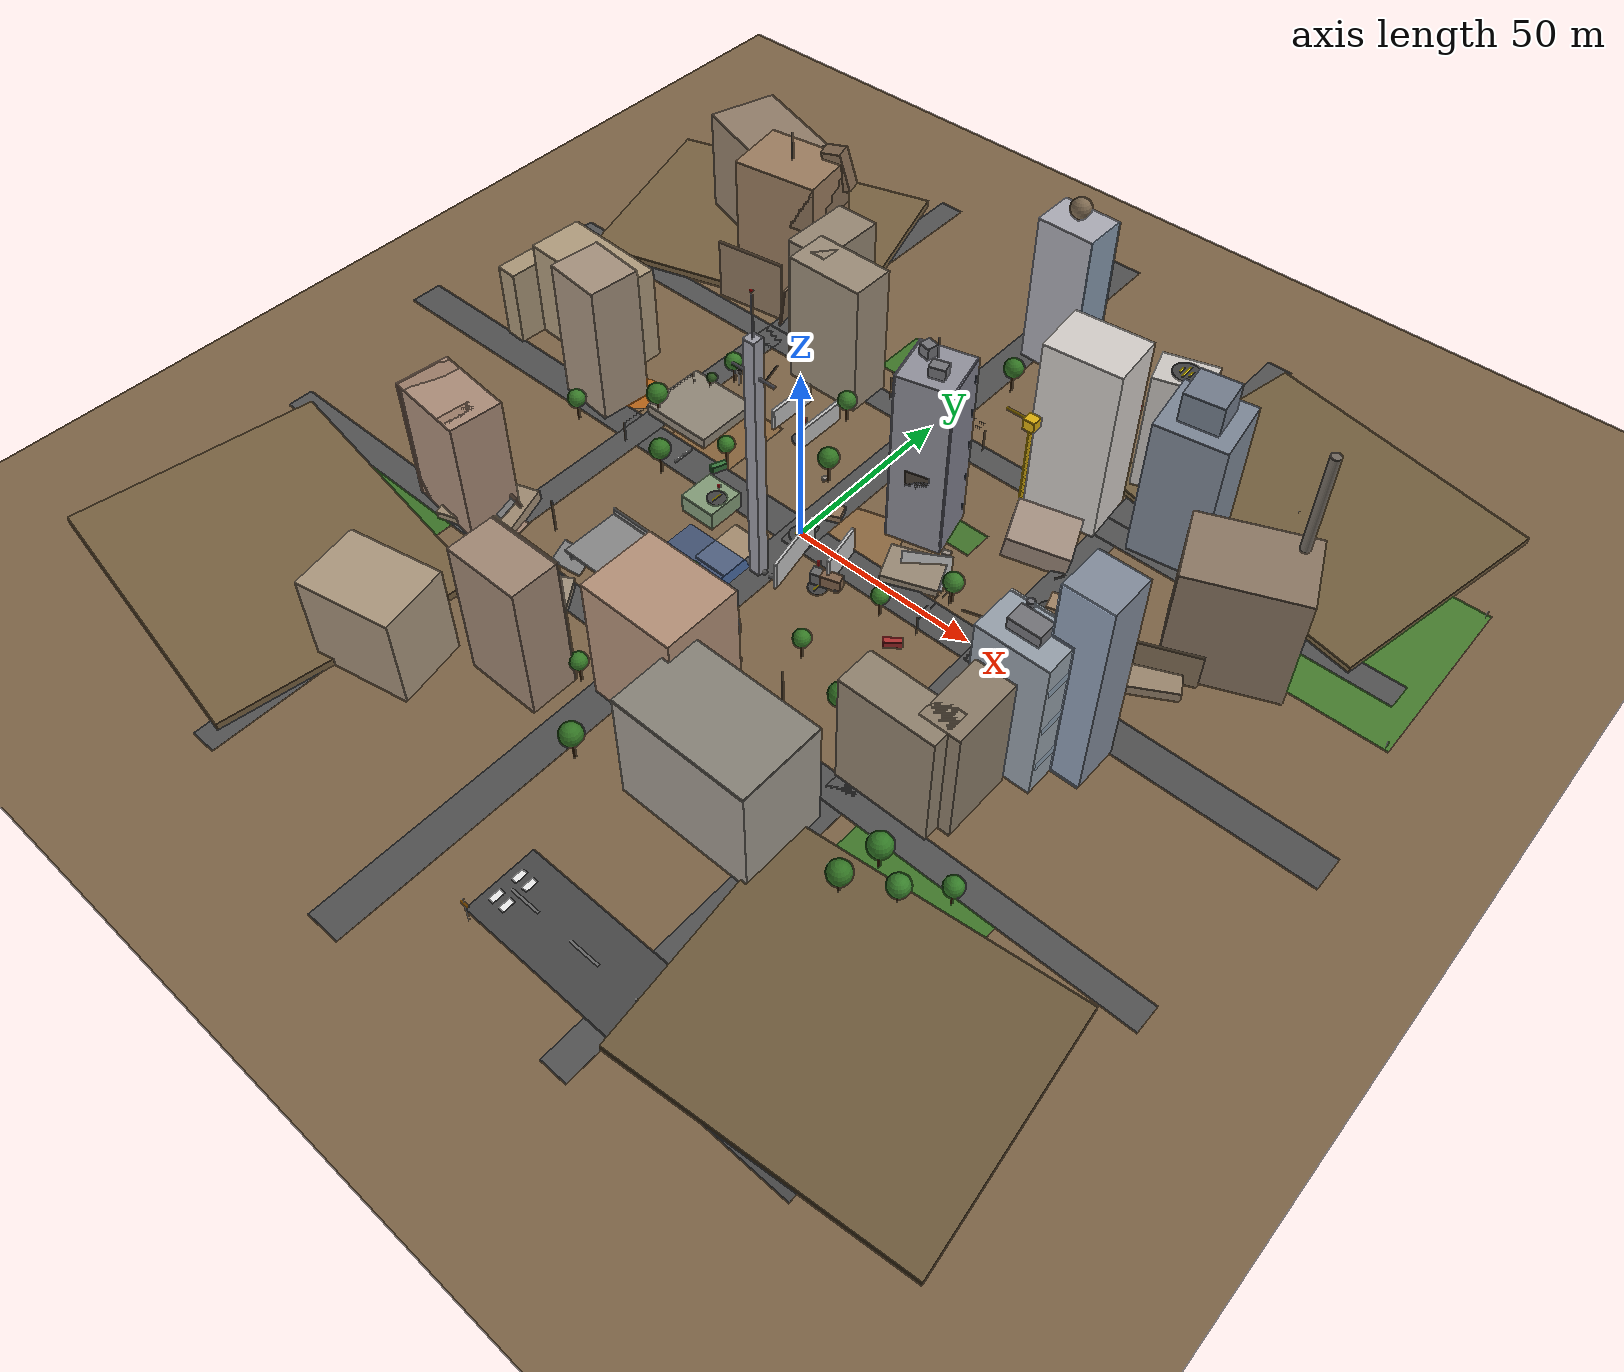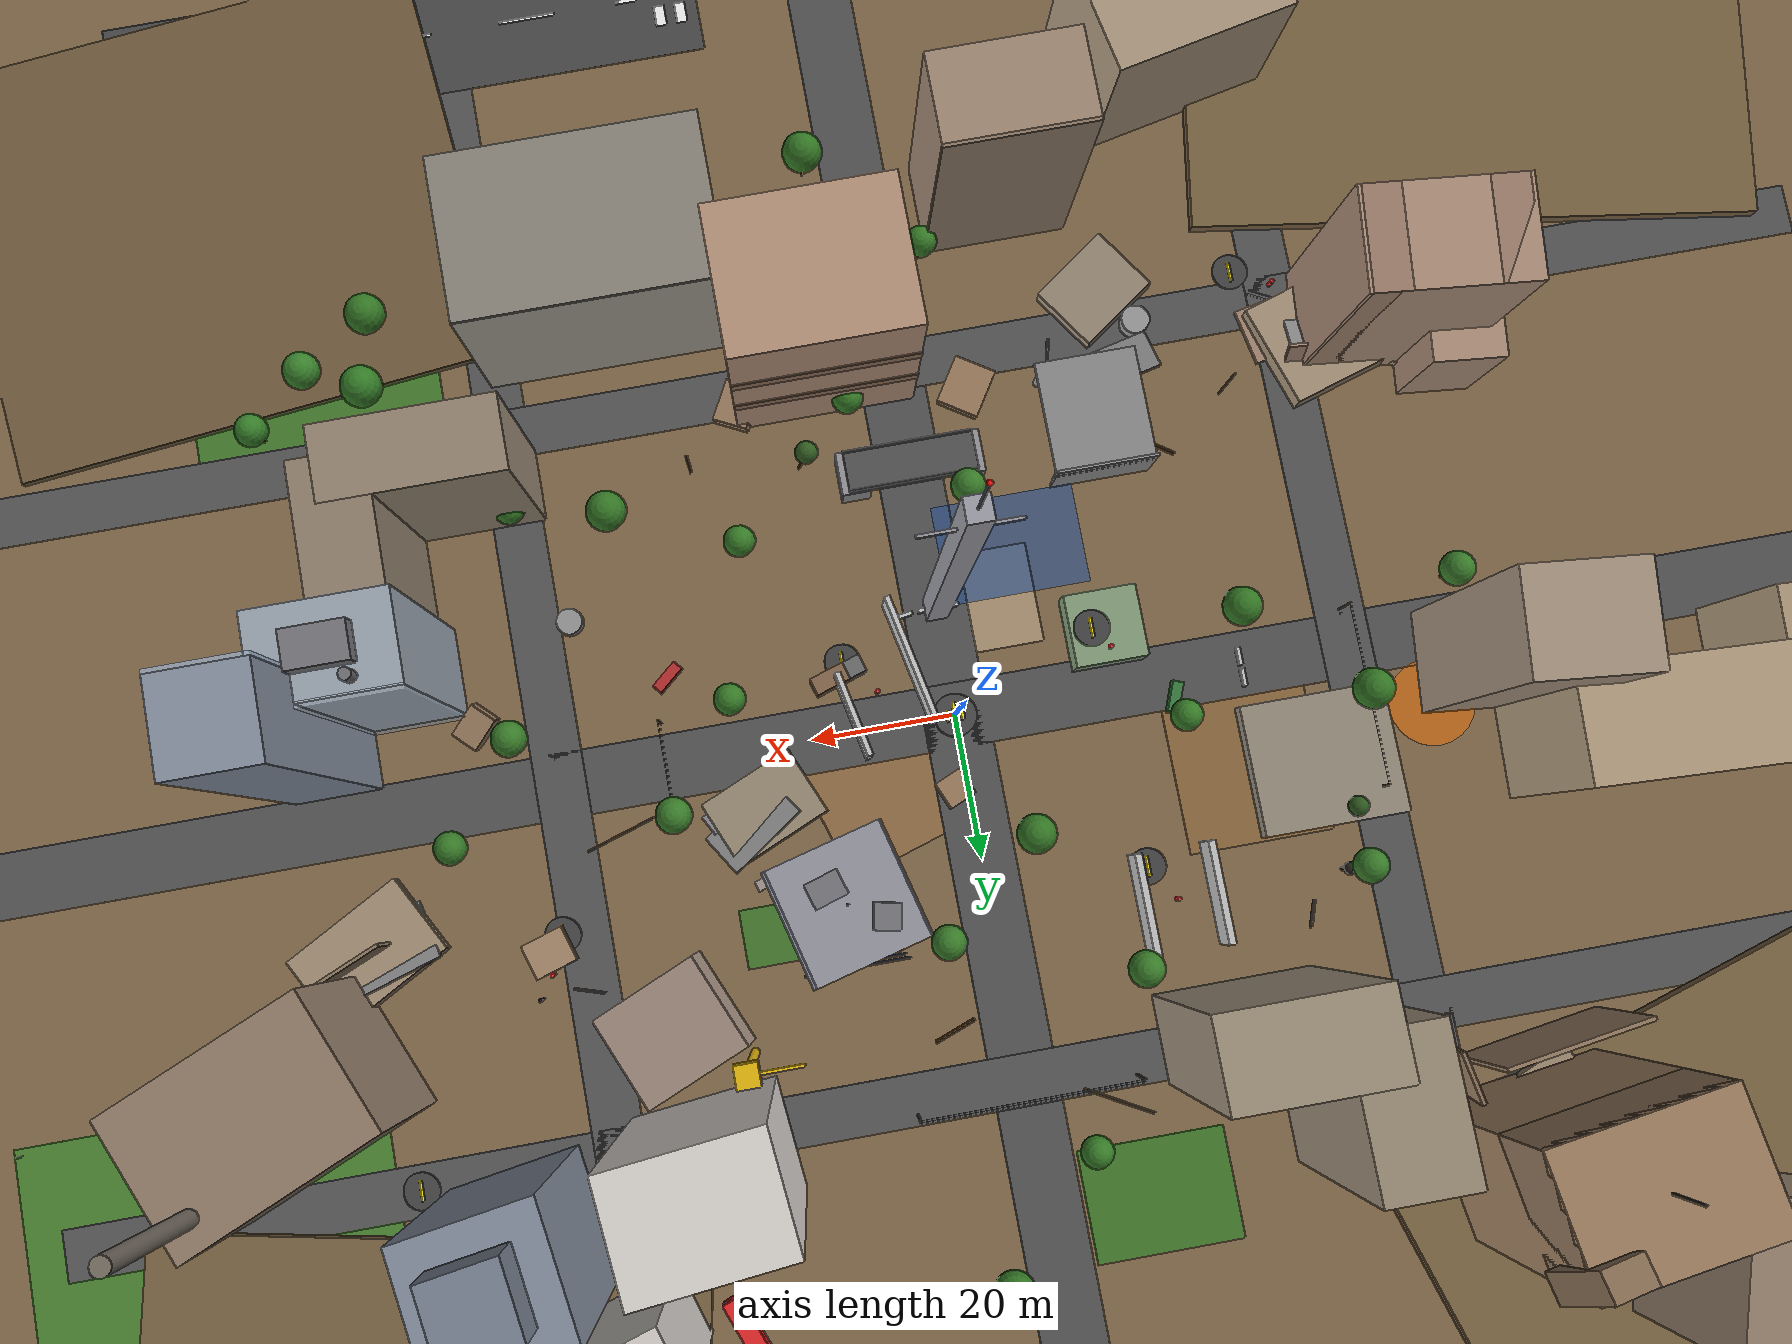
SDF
<sdf version="1.9">
 <world name="p110_world">
  <physics type="ode">
   <max_step_size>0.004</max_step_size>
   <real_time_factor>1.0</real_time_factor>
   <real_time_update_rate>250</real_time_update_rate>
  </physics>
  <gravity>0 0 -9.8</gravity>
  <magnetic_field>6e-06 2.3e-05 -4.2e-05</magnetic_field>
  <spherical_coordinates>
   <surface_model>EARTH_WGS84</surface_model>
   <world_frame_orientation>ENU</world_frame_orientation>
   <latitude_deg>34.0572</latitude_deg>
   <longitude_deg>-117.8227</longitude_deg>
   <elevation>305</elevation>
  </spherical_coordinates>
  <scene>
   <ambient>0.45 0.45 0.50 1.0</ambient>
   <background>0.55 0.70 0.85 1.0</background>
   <shadows>true</shadows>
   <sky>
    <time>10</time>
    <sunrise>6</sunrise>
    <sunset>20</sunset>
    <clouds><speed>8</speed><mean_size>0.5</mean_size><ambient>0.82 0.82 0.82 1</ambient></clouds>
   </sky>
   <fog>
    <color>0.78 0.82 0.88 1</color>
    <type>linear</type>
    <start>80</start>
    <end>300</end>
    <density>0.008</density>
   </fog>
  </scene>
  <atmosphere type="adiabatic">
   <temperature>295</temperature>
   <pressure>101325</pressure>
   <temperature_gradient>-0.0065</temperature_gradient>
  </atmosphere>
  <light type="directional" name="sun">
   <pose>50 80 100 0 0 0</pose>
   <diffuse>1.0 0.98 0.92 1</diffuse>
   <specular>0.8 0.78 0.72 1</specular>
   <direction>-0.4 -0.3 -0.9</direction>
  </light>
  <light type="directional" name="sky_fill">
   <cast_shadows>false</cast_shadows>
   <pose>0 0 50 0 0 0</pose>
   <diffuse>0.35 0.42 0.55 1</diffuse>
   <specular>0.0 0.0 0.0 1</specular>
   <direction>0.1 0.1 -1</direction>
  </light>
  <model name="ground_base">
   <static>true</static>
   <link name="link">
    <collision name="c"><geometry><plane><normal>0 0 1</normal><size>700 700</size></plane></geometry></collision>
    <visual name="v">
     <geometry><plane><normal>0 0 1</normal><size>700 700</size></plane></geometry>
     <material>
      <ambient>0.42 0.34 0.24 1</ambient>
      <diffuse>0.50 0.40 0.28 1</diffuse>
      <specular>0.05 0.04 0.03 1</specular>
     </material>
    </visual>
   </link>
  </model>
  <model name="tmound_nw">
   <static>true</static>
   <pose>-90 85 1.1 0 0 0.3</pose>
   <link name="link">
    <collision name="c"><geometry><box><size>80 60 2.2</size></box></geometry></collision>
    <visual name="v">
     <geometry><box><size>80 60 2.2</size></box></geometry>
     <material><ambient>0.40 0.33 0.22 1</ambient><diffuse>0.48 0.39 0.26 1</diffuse></material>
    </visual>
   </link>
  </model>
  <model name="tmound_ne">
   <static>true</static>
   <pose>88 88 0.9 0 0 -0.2</pose>
   <link name="link">
    <collision name="c"><geometry><box><size>75 65 1.8</size></box></geometry></collision>
    <visual name="v">
     <geometry><box><size>75 65 1.8</size></box></geometry>
     <material><ambient>0.38 0.32 0.21 1</ambient><diffuse>0.46 0.38 0.25 1</diffuse></material>
    </visual>
   </link>
  </model>
  <model name="tmound_se">
   <static>true</static>
   <pose>90 -88 0.7 0 0 0.1</pose>
   <link name="link">
    <collision name="c"><geometry><box><size>70 60 1.4</size></box></geometry></collision>
    <visual name="v">
     <geometry><box><size>70 60 1.4</size></box></geometry>
     <material><ambient>0.36 0.30 0.20 1</ambient><diffuse>0.44 0.36 0.24 1</diffuse></material>
    </visual>
   </link>
  </model>
  <model name="tmound_sw">
   <static>true</static>
   <pose>-90 -88 1.0 0 0 -0.15</pose>
   <link name="link">
    <collision name="c"><geometry><box><size>80 65 2.0</size></box></geometry></collision>
    <visual name="v">
     <geometry><box><size>80 65 2.0</size></box></geometry>
     <material><ambient>0.40 0.33 0.22 1</ambient><diffuse>0.48 0.39 0.26 1</diffuse></material>
    </visual>
   </link>
  </model>
  <model name="road_ew_main">
   <static>true</static>
   <pose>0 0 0.05 0 0 0</pose>
   <link name="link">
    <visual name="v">
     <geometry><box><size>280 9 0.08</size></box></geometry>
     <material>
      <ambient>0.26 0.26 0.26 1</ambient>
      <diffuse>0.32 0.32 0.32 1</diffuse>
      <specular>0.10 0.10 0.10 1</specular>
     </material>
    </visual>
   </link>
  </model>
  <model name="road_ew_n">
   <static>true</static>
   <pose>0 50 0.05 0 0 0</pose>
   <link name="link">
    <visual name="v">
     <geometry><box><size>260 7 0.08</size></box></geometry>
     <material>
      <ambient>0.27 0.27 0.27 1</ambient>
      <diffuse>0.33 0.33 0.33 1</diffuse>
      <specular>0.10 0.10 0.10 1</specular>
     </material>
    </visual>
   </link>
  </model>
  <model name="road_ew_s">
   <static>true</static>
   <pose>0 -50 0.05 0 0 0</pose>
   <link name="link">
    <visual name="v">
     <geometry><box><size>260 7 0.08</size></box></geometry>
     <material>
      <ambient>0.27 0.27 0.27 1</ambient>
      <diffuse>0.33 0.33 0.33 1</diffuse>
      <specular>0.10 0.10 0.10 1</specular>
     </material>
    </visual>
   </link>
  </model>
  <model name="road_ns_main">
   <static>true</static>
   <pose>0 0 0.05 0 0 0</pose>
   <link name="link">
    <visual name="v">
     <geometry><box><size>9 280 0.08</size></box></geometry>
     <material>
      <ambient>0.26 0.26 0.26 1</ambient>
      <diffuse>0.32 0.32 0.32 1</diffuse>
      <specular>0.10 0.10 0.10 1</specular>
     </material>
    </visual>
   </link>
  </model>
  <model name="road_ns_e">
   <static>true</static>
   <pose>55 0 0.05 0 0 0</pose>
   <link name="link">
    <visual name="v">
     <geometry><box><size>7 260 0.08</size></box></geometry>
     <material>
      <ambient>0.27 0.27 0.27 1</ambient>
      <diffuse>0.33 0.33 0.33 1</diffuse>
      <specular>0.10 0.10 0.10 1</specular>
     </material>
    </visual>
   </link>
  </model>
  <model name="road_ns_w">
   <static>true</static>
   <pose>-55 0 0.05 0 0 0</pose>
   <link name="link">
    <visual name="v">
     <geometry><box><size>7 260 0.08</size></box></geometry>
     <material>
      <ambient>0.27 0.27 0.27 1</ambient>
      <diffuse>0.33 0.33 0.33 1</diffuse>
      <specular>0.10 0.10 0.10 1</specular>
     </material>
    </visual>
   </link>
  </model>
  <model name="grass_park_se">
   <static>true</static>
   <pose>80 -65 0.05 0 0 0</pose>
   <link name="link">
    <visual name="v">
     <geometry><box><size>35 30 0.06</size></box></geometry>
     <material><ambient>0.22 0.40 0.14 1</ambient><diffuse>0.26 0.48 0.17 1</diffuse></material>
    </visual>
   </link>
  </model>
  <model name="grass_park_sw">
   <static>true</static>
   <pose>-80 -65 0.05 0 0 0</pose>
   <link name="link">
    <visual name="v">
     <geometry><box><size>30 25 0.06</size></box></geometry>
     <material><ambient>0.20 0.38 0.13 1</ambient><diffuse>0.24 0.46 0.16 1</diffuse></material>
    </visual>
   </link>
  </model>
  <model name="grass_courtyard_n">
   <static>true</static>
   <pose>-15 68 0.05 0 0 0</pose>
   <link name="link">
    <visual name="v">
     <geometry><box><size>20 15 0.06</size></box></geometry>
     <material><ambient>0.21 0.39 0.13 1</ambient><diffuse>0.25 0.47 0.16 1</diffuse></material>
    </visual>
   </link>
  </model>
  <model name="grass_median">
   <static>true</static>
   <pose>28 25 0.05 0 0 0</pose>
   <link name="link">
    <visual name="v">
     <geometry><box><size>12 8 0.06</size></box></geometry>
     <material><ambient>0.22 0.38 0.14 1</ambient><diffuse>0.26 0.46 0.17 1</diffuse></material>
    </visual>
   </link>
  </model>
  <model name="dirt_blast_c">
   <static>true</static>
   <pose>10 8 0.05 0 0 0.3</pose>
   <link name="link">
    <visual name="v">
     <geometry><box><size>22 18 0.06</size></box></geometry>
     <material><ambient>0.48 0.36 0.22 1</ambient><diffuse>0.56 0.42 0.26 1</diffuse></material>
    </visual>
   </link>
  </model>
  <model name="dirt_blast_w">
   <static>true</static>
   <pose>-38 12 0.05 0 0 0</pose>
   <link name="link">
    <visual name="v">
     <geometry><box><size>20 25 0.06</size></box></geometry>
     <material><ambient>0.46 0.34 0.20 1</ambient><diffuse>0.54 0.40 0.24 1</diffuse></material>
    </visual>
   </link>
  </model>
  <model name="rubble_ground_c">
   <static>true</static>
   <pose>-5 -15 0.05 0 0 0</pose>
   <link name="link">
    <visual name="v">
     <geometry><box><size>18 14 0.06</size></box></geometry>
     <material><ambient>0.58 0.50 0.38 1</ambient><diffuse>0.66 0.56 0.44 1</diffuse></material>
    </visual>
   </link>
  </model>
  <model name="flood_zone">
   <static>true</static>
   <pose>-12 -22 0.06 0 0 0</pose>
   <link name="link">
    <visual name="v">
     <geometry><box><size>20 14 0.12</size></box></geometry>
     <material>
      <ambient>0.14 0.28 0.52 0.65</ambient>
      <diffuse>0.18 0.34 0.60 0.65</diffuse>
      <specular>0.50 0.55 0.62 1</specular>
     </material>
    </visual>
   </link>
  </model>
  <model name="warehouse_1">
   <static>true</static>
   <pose>-65 70 21 0 0 0.15</pose>
   <link name="link">
    <collision name="c"><geometry><box><size>24 18 42</size></box></geometry></collision>
    <visual name="main">
     <geometry><box><size>24 18 42</size></box></geometry>
     <material>
      <ambient>0.55 0.45 0.35 1</ambient>
      <diffuse>0.62 0.50 0.38 1</diffuse>
      <specular>0.10 0.10 0.10 1</specular>
     </material>
    </visual>
    <visual name="upper_damage">
     <pose>0 0 14 0 0 0</pose>
     <geometry><box><size>24 18 14</size></box></geometry>
     <material><ambient>0.48 0.40 0.32 1</ambient><diffuse>0.55 0.45 0.35 1</diffuse></material>
    </visual>
    <visual name="corner_break">
     <pose>10 7 18 0.15 -0.2 0</pose>
     <geometry><box><size>6 4 12</size></box></geometry>
     <material><ambient>0.44 0.36 0.28 1</ambient><diffuse>0.52 0.42 0.32 1</diffuse></material>
    </visual>
   </link>
  </model>
  <model name="office_tower">
   <static>true</static>
   <pose>20 22 25 0 0 0.25</pose>
   <link name="link">
    <collision name="c"><geometry><box><size>14 14 50</size></box></geometry></collision>
    <visual name="main">
     <geometry><box><size>14 14 50</size></box></geometry>
     <material>
      <ambient>0.50 0.50 0.52 1</ambient>
      <diffuse>0.58 0.58 0.62 1</diffuse>
      <specular>0.18 0.18 0.20 1</specular>
     </material>
    </visual>
    <visual name="face_e">
     <pose>7 0 0 0 0 0</pose>
     <geometry><box><size>0.4 14 50</size></box></geometry>
     <material>
      <ambient>0.44 0.44 0.48 1</ambient>
      <diffuse>0.50 0.50 0.56 1</diffuse>
      <specular>0.20 0.20 0.22 1</specular>
     </material>
    </visual>
    <visual name="face_w">
     <pose>-7 0 0 0 0 0</pose>
     <geometry><box><size>0.4 14 50</size></box></geometry>
     <material>
      <ambient>0.44 0.44 0.48 1</ambient>
      <diffuse>0.50 0.50 0.56 1</diffuse>
      <specular>0.20 0.20 0.22 1</specular>
     </material>
    </visual>
    <visual name="blast_hole">
     <pose>0 -6.5 -6 0 0 0</pose>
     <geometry><box><size>6 1 8</size></box></geometry>
     <material><ambient>0.25 0.22 0.20 1</ambient><diffuse>0.30 0.26 0.22 1</diffuse></material>
    </visual>
   </link>
  </model>
  <model name="modern_building">
   <static>true</static>
   <pose>75 -18 20 0 0 0</pose>
   <link name="link">
    <collision name="c"><geometry><box><size>18 12 40</size></box></geometry></collision>
    <visual name="main">
     <geometry><box><size>18 12 40</size></box></geometry>
     <material>
      <ambient>0.52 0.56 0.58 1</ambient>
      <diffuse>0.60 0.64 0.68 1</diffuse>
      <specular>0.22 0.22 0.24 1</specular>
     </material>
    </visual>
    <visual name="glass_n">
     <pose>0 6.2 0 0 0 0</pose>
     <geometry><box><size>18 0.8 40</size></box></geometry>
     <material>
      <ambient>0.65 0.70 0.75 0.7</ambient>
      <diffuse>0.70 0.75 0.80 0.7</diffuse>
      <specular>0.40 0.40 0.40 1</specular>
     </material>
    </visual>
   </link>
  </model>
  <model name="residential_1">
   <static>true</static>
   <pose>-68 -45 17.5 0 0 -0.1</pose>
   <link name="link">
    <collision name="c"><geometry><box><size>22 14 35</size></box></geometry></collision>
    <visual name="main">
     <geometry><box><size>22 14 35</size></box></geometry>
     <material>
      <ambient>0.58 0.48 0.42 1</ambient>
      <diffuse>0.68 0.56 0.48 1</diffuse>
      <specular>0.12 0.10 0.10 1</specular>
     </material>
    </visual>
    <visual name="unit_l">
     <pose>-8 0 0 0 0 0</pose>
     <geometry><box><size>5 14 35</size></box></geometry>
     <material><ambient>0.52 0.44 0.38 1</ambient><diffuse>0.62 0.50 0.42 1</diffuse></material>
    </visual>
    <visual name="unit_r">
     <pose>8 0 0 0 0 0</pose>
     <geometry><box><size>5 14 35</size></box></geometry>
     <material><ambient>0.52 0.44 0.38 1</ambient><diffuse>0.62 0.50 0.42 1</diffuse></material>
    </visual>
   </link>
  </model>
  <model name="clinic">
   <static>true</static>
   <pose>55 72 18 0 0 0.3</pose>
   <link name="link">
    <collision name="c"><geometry><box><size>14 10 36</size></box></geometry></collision>
    <visual name="main">
     <geometry><box><size>14 10 36</size></box></geometry>
     <material>
      <ambient>0.72 0.70 0.68 1</ambient>
      <diffuse>0.82 0.80 0.78 1</diffuse>
      <specular>0.18 0.18 0.18 1</specular>
     </material>
    </visual>
    <visual name="cross_h">
     <pose>0 5.2 8 0 0 0</pose>
     <geometry><box><size>4 0.3 1</size></box></geometry>
     <material><ambient>0.85 0.12 0.12 1</ambient><diffuse>0.90 0.15 0.15 1</diffuse></material>
    </visual>
    <visual name="cross_v">
     <pose>0 5.2 8 0 0 0</pose>
     <geometry><box><size>1 0.3 4</size></box></geometry>
     <material><ambient>0.85 0.12 0.12 1</ambient><diffuse>0.90 0.15 0.15 1</diffuse></material>
    </visual>
   </link>
  </model>
  <model name="apartment_s">
   <static>true</static>
   <pose>-18 -72 19 0 0 0</pose>
   <link name="link">
    <collision name="c"><geometry><box><size>20 12 38</size></box></geometry></collision>
    <visual name="main">
     <geometry><box><size>20 12 38</size></box></geometry>
     <material>
      <ambient>0.54 0.46 0.40 1</ambient>
      <diffuse>0.64 0.54 0.46 1</diffuse>
      <specular>0.10 0.10 0.10 1</specular>
     </material>
    </visual>
    <visual name="balconies">
     <pose>0 6.2 0 0 0 0</pose>
     <geometry><box><size>20 0.6 38</size></box></geometry>
     <material><ambient>0.48 0.42 0.36 1</ambient><diffuse>0.56 0.48 0.40 1</diffuse></material>
    </visual>
   </link>
  </model>
  <model name="factory_e">
   <static>true</static>
   <pose>95 35 16 0 0 0.4</pose>
   <link name="link">
    <collision name="c"><geometry><box><size>28 20 32</size></box></geometry></collision>
    <visual name="main">
     <geometry><box><size>28 20 32</size></box></geometry>
     <material>
      <ambient>0.48 0.42 0.34 1</ambient>
      <diffuse>0.56 0.48 0.40 1</diffuse>
      <specular>0.08 0.08 0.08 1</specular>
     </material>
    </visual>
    <visual name="stack">
     <pose>10 6 25 0 0 0</pose>
     <geometry><cylinder><radius>1.2</radius><length>36</length></cylinder></geometry>
     <material><ambient>0.38 0.35 0.32 1</ambient><diffuse>0.45 0.42 0.38 1</diffuse></material>
    </visual>
   </link>
  </model>
  <model name="school_w">
   <static>true</static>
   <pose>-88 18 14 0 0 -0.05</pose>
   <link name="link">
    <collision name="c"><geometry><box><size>30 15 28</size></box></geometry></collision>
    <visual name="main">
     <geometry><box><size>30 15 28</size></box></geometry>
     <material>
      <ambient>0.60 0.54 0.44 1</ambient>
      <diffuse>0.70 0.62 0.50 1</diffuse>
      <specular>0.12 0.12 0.10 1</specular>
     </material>
    </visual>
    <visual name="wing">
     <pose>-18 -8 -3 0 0 0</pose>
     <geometry><box><size>6 14 22</size></box></geometry>
     <material><ambient>0.58 0.52 0.42 1</ambient><diffuse>0.68 0.60 0.48 1</diffuse></material>
    </visual>
   </link>
  </model>
  <model name="shopping_se">
   <static>true</static>
   <pose>38 -68 15 0 0 0</pose>
   <link name="link">
    <collision name="c"><geometry><box><size>35 22 30</size></box></geometry></collision>
    <visual name="main">
     <geometry><box><size>35 22 30</size></box></geometry>
     <material>
      <ambient>0.56 0.54 0.50 1</ambient>
      <diffuse>0.65 0.62 0.58 1</diffuse>
      <specular>0.15 0.15 0.14 1</specular>
     </material>
    </visual>
    <visual name="canopy">
     <pose>0 0 15.2 0 0 0</pose>
     <geometry><box><size>35 22 0.4</size></box></geometry>
     <material><ambient>0.45 0.44 0.40 1</ambient><diffuse>0.54 0.52 0.48 1</diffuse></material>
    </visual>
   </link>
  </model>
  <model name="hotel_n">
   <static>true</static>
   <pose>8 95 22 0 0 0</pose>
   <link name="link">
    <collision name="c"><geometry><box><size>16 12 44</size></box></geometry></collision>
    <visual name="main">
     <geometry><box><size>16 12 44</size></box></geometry>
     <material>
      <ambient>0.60 0.60 0.62 1</ambient>
      <diffuse>0.68 0.68 0.72 1</diffuse>
      <specular>0.22 0.22 0.24 1</specular>
     </material>
    </visual>
    <visual name="glass_e">
     <pose>8.2 0 0 0 0 0</pose>
     <geometry><box><size>0.6 12 44</size></box></geometry>
     <material>
      <ambient>0.50 0.60 0.70 0.7</ambient>
      <diffuse>0.55 0.65 0.75 0.7</diffuse>
      <specular>0.35 0.35 0.40 1</specular>
     </material>
    </visual>
   </link>
  </model>
  <model name="community_s">
   <static>true</static>
   <pose>-45 -88 12.5 0 0 0.2</pose>
   <link name="link">
    <collision name="c"><geometry><box><size>25 18 25</size></box></geometry></collision>
    <visual name="main">
     <geometry><box><size>25 18 25</size></box></geometry>
     <material>
      <ambient>0.58 0.52 0.44 1</ambient>
      <diffuse>0.68 0.60 0.50 1</diffuse>
      <specular>0.10 0.10 0.08 1</specular>
     </material>
    </visual>
   </link>
  </model>
  <model name="warehouse_2">
   <static>true</static>
   <pose>-90 88 16 0 0 -0.3</pose>
   <link name="link">
    <collision name="c"><geometry><box><size>30 20 32</size></box></geometry></collision>
    <visual name="main">
     <geometry><box><size>30 20 32</size></box></geometry>
     <material>
      <ambient>0.50 0.44 0.36 1</ambient>
      <diffuse>0.58 0.50 0.42 1</diffuse>
      <specular>0.08 0.08 0.08 1</specular>
     </material>
    </visual>
   </link>
  </model>
  <model name="col1_wall_s">
   <static>true</static>
   <pose>-68 56 9 0 0 0.15</pose>
   <link name="link">
    <collision name="c"><geometry><box><size>20 0.6 18</size></box></geometry></collision>
    <visual name="v">
     <geometry><box><size>20 0.6 18</size></box></geometry>
     <material><ambient>0.50 0.42 0.34 1</ambient><diffuse>0.58 0.48 0.38 1</diffuse></material>
    </visual>
   </link>
  </model>
  <model name="col1_wall_e">
   <static>true</static>
   <pose>-57 62 6 0 0.12 0.18</pose>
   <link name="link">
    <collision name="c"><geometry><box><size>0.6 14 12</size></box></geometry></collision>
    <visual name="v">
     <geometry><box><size>0.6 14 12</size></box></geometry>
     <material><ambient>0.48 0.40 0.32 1</ambient><diffuse>0.56 0.46 0.36 1</diffuse></material>
    </visual>
   </link>
  </model>
  <model name="col1_slab1">
   <static>true</static>
   <pose>-62 66 2.2 0.45 0.05 0.2</pose>
   <link name="link">
    <collision name="c"><geometry><box><size>16 10 0.4</size></box></geometry></collision>
    <visual name="v">
     <geometry><box><size>16 10 0.4</size></box></geometry>
     <material>
      <ambient>0.46 0.46 0.46 1</ambient>
      <diffuse>0.54 0.54 0.54 1</diffuse>
      <specular>0.08 0.08 0.08 1</specular>
     </material>
    </visual>
   </link>
  </model>
  <model name="col1_slab2">
   <static>true</static>
   <pose>-70 68 1.2 -0.55 0.08 0.25</pose>
   <link name="link">
    <collision name="c"><geometry><box><size>14 8 0.4</size></box></geometry></collision>
    <visual name="v">
     <geometry><box><size>14 8 0.4</size></box></geometry>
     <material><ambient>0.44 0.44 0.44 1</ambient><diffuse>0.52 0.52 0.52 1</diffuse></material>
    </visual>
   </link>
  </model>
  <model name="col1_wall_fallen">
   <static>true</static>
   <pose>-64 72 0.5 1.5708 0.1 0.3</pose>
   <link name="link">
    <collision name="c"><geometry><box><size>12 0.5 6</size></box></geometry></collision>
    <visual name="v">
     <geometry><box><size>12 0.5 6</size></box></geometry>
     <material><ambient>0.50 0.42 0.34 1</ambient><diffuse>0.58 0.48 0.38 1</diffuse></material>
    </visual>
   </link>
  </model>
  <model name="col1_rubble_a">
   <static>true</static>
   <pose>-66 68 1.8 0.1 0.05 0.4</pose>
   <link name="link">
    <collision name="c"><geometry><box><size>18 14 3.5</size></box></geometry></collision>
    <visual name="v">
     <geometry><box><size>18 14 3.5</size></box></geometry>
     <material><ambient>0.54 0.48 0.40 1</ambient><diffuse>0.62 0.54 0.44 1</diffuse></material>
    </visual>
   </link>
  </model>
  <model name="col1_rubble_b">
   <static>true</static>
   <pose>-72 70 0.8 0.08 -0.06 -0.3</pose>
   <link name="link">
    <collision name="c"><geometry><box><size>10 8 1.5</size></box></geometry></collision>
    <visual name="v">
     <geometry><box><size>10 8 1.5</size></box></geometry>
     <material><ambient>0.56 0.50 0.42 1</ambient><diffuse>0.64 0.56 0.46 1</diffuse></material>
    </visual>
   </link>
  </model>
  <model name="col1_rebar1">
   <static>true</static>
   <pose>-60 66 3.5 0 0.4 0.8</pose>
   <link name="link">
    <visual name="v">
     <geometry><box><size>0.12 0.12 5</size></box></geometry>
     <material>
      <ambient>0.28 0.25 0.22 1</ambient>
      <diffuse>0.35 0.32 0.28 1</diffuse>
      <specular>0.45 0.42 0.38 1</specular>
     </material>
    </visual>
   </link>
  </model>
  <model name="col1_rebar2">
   <static>true</static>
   <pose>-68 70 3.0 0 0.5 -0.5</pose>
   <link name="link">
    <visual name="v">
     <geometry><box><size>0.12 0.12 4</size></box></geometry>
     <material>
      <ambient>0.28 0.25 0.22 1</ambient>
      <diffuse>0.35 0.32 0.28 1</diffuse>
      <specular>0.45 0.42 0.38 1</specular>
     </material>
    </visual>
   </link>
  </model>
  <model name="col2_corner">
   <static>true</static>
   <pose>-75 -38 8 0 0 -0.1</pose>
   <link name="link">
    <collision name="c"><geometry><box><size>10 10 16</size></box></geometry></collision>
    <visual name="v">
     <geometry><box><size>10 10 16</size></box></geometry>
     <material><ambient>0.58 0.48 0.42 1</ambient><diffuse>0.68 0.56 0.48 1</diffuse></material>
    </visual>
   </link>
  </model>
  <model name="col2_slab1">
   <static>true</static>
   <pose>-62 -44 3.5 0.50 0 -0.1</pose>
   <link name="link">
    <collision name="c"><geometry><box><size>14 9 0.35</size></box></geometry></collision>
    <visual name="v">
     <geometry><box><size>14 9 0.35</size></box></geometry>
     <material><ambient>0.45 0.45 0.45 1</ambient><diffuse>0.54 0.54 0.54 1</diffuse></material>
    </visual>
   </link>
  </model>
  <model name="col2_slab2">
   <static>true</static>
   <pose>-60 -42 1.6 0.30 0.05 -0.15</pose>
   <link name="link">
    <collision name="c"><geometry><box><size>12 8 0.35</size></box></geometry></collision>
    <visual name="v">
     <geometry><box><size>12 8 0.35</size></box></geometry>
     <material><ambient>0.43 0.43 0.43 1</ambient><diffuse>0.52 0.52 0.52 1</diffuse></material>
    </visual>
   </link>
  </model>
  <model name="col2_wall_lean">
   <static>true</static>
   <pose>-58 -40 3.5 0.3 0 -0.08</pose>
   <link name="link">
    <collision name="c"><geometry><box><size>8 0.5 7</size></box></geometry></collision>
    <visual name="v">
     <geometry><box><size>8 0.5 7</size></box></geometry>
     <material><ambient>0.56 0.46 0.40 1</ambient><diffuse>0.66 0.54 0.46 1</diffuse></material>
    </visual>
   </link>
  </model>
  <model name="col2_wall_flat">
   <static>true</static>
   <pose>-55 -46 0.6 1.5708 0 0.2</pose>
   <link name="link">
    <collision name="c"><geometry><box><size>10 0.5 8</size></box></geometry></collision>
    <visual name="v">
     <geometry><box><size>10 0.5 8</size></box></geometry>
     <material><ambient>0.54 0.44 0.38 1</ambient><diffuse>0.64 0.52 0.44 1</diffuse></material>
    </visual>
   </link>
  </model>
  <model name="col2_rubble">
   <static>true</static>
   <pose>-62 -44 1.5 0.06 -0.04 0.3</pose>
   <link name="link">
    <collision name="c"><geometry><box><size>20 15 3.0</size></box></geometry></collision>
    <visual name="v">
     <geometry><box><size>20 15 3.0</size></box></geometry>
     <material><ambient>0.56 0.50 0.42 1</ambient><diffuse>0.64 0.56 0.46 1</diffuse></material>
    </visual>
   </link>
  </model>
  <model name="col2_rubble_b">
   <static>true</static>
   <pose>-70 -42 0.8 0.05 0.05 -0.5</pose>
   <link name="link">
    <collision name="c"><geometry><box><size>10 8 1.5</size></box></geometry></collision>
    <visual name="v">
     <geometry><box><size>10 8 1.5</size></box></geometry>
     <material><ambient>0.54 0.48 0.40 1</ambient><diffuse>0.62 0.54 0.44 1</diffuse></material>
    </visual>
   </link>
  </model>
  <model name="col3_slab1">
   <static>true</static>
   <pose>30 10 1.8 0.40 0.06 0.6</pose>
   <link name="link">
    <collision name="c"><geometry><box><size>12 7 0.4</size></box></geometry></collision>
    <visual name="v">
     <geometry><box><size>12 7 0.4</size></box></geometry>
     <material><ambient>0.46 0.46 0.46 1</ambient><diffuse>0.55 0.55 0.55 1</diffuse></material>
    </visual>
   </link>
  </model>
  <model name="col3_facade">
   <static>true</static>
   <pose>32 8 0.8 1.5708 0.1 0.5</pose>
   <link name="link">
    <collision name="c"><geometry><box><size>8 0.4 5</size></box></geometry></collision>
    <visual name="v">
     <geometry><box><size>8 0.4 5</size></box></geometry>
     <material>
      <ambient>0.48 0.48 0.50 1</ambient>
      <diffuse>0.56 0.56 0.58 1</diffuse>
      <specular>0.20 0.20 0.22 1</specular>
     </material>
    </visual>
   </link>
  </model>
  <model name="col3_rubble">
   <static>true</static>
   <pose>28 8 1.2 0.05 0.04 0.4</pose>
   <link name="link">
    <collision name="c"><geometry><box><size>14 10 2.4</size></box></geometry></collision>
    <visual name="v">
     <geometry><box><size>14 10 2.4</size></box></geometry>
     <material><ambient>0.52 0.48 0.42 1</ambient><diffuse>0.60 0.54 0.46 1</diffuse></material>
    </visual>
   </link>
  </model>
  <model name="col4_wall_n">
   <static>true</static>
   <pose>88 20 5 0 0 0.4</pose>
   <link name="link">
    <collision name="c"><geometry><box><size>16 0.5 10</size></box></geometry></collision>
    <visual name="v">
     <geometry><box><size>16 0.5 10</size></box></geometry>
     <material><ambient>0.46 0.40 0.32 1</ambient><diffuse>0.54 0.46 0.36 1</diffuse></material>
    </visual>
   </link>
  </model>
  <model name="col4_slab">
   <static>true</static>
   <pose>82 18 1.5 0.42 0 0.3</pose>
   <link name="link">
    <collision name="c"><geometry><box><size>14 9 0.4</size></box></geometry></collision>
    <visual name="v">
     <geometry><box><size>14 9 0.4</size></box></geometry>
     <material><ambient>0.44 0.44 0.44 1</ambient><diffuse>0.52 0.52 0.52 1</diffuse></material>
    </visual>
   </link>
  </model>
  <model name="col4_rubble">
   <static>true</static>
   <pose>84 18 1.4 0.04 -0.03 0.5</pose>
   <link name="link">
    <collision name="c"><geometry><box><size>18 12 2.8</size></box></geometry></collision>
    <visual name="v">
     <geometry><box><size>18 12 2.8</size></box></geometry>
     <material><ambient>0.54 0.48 0.40 1</ambient><diffuse>0.62 0.54 0.44 1</diffuse></material>
    </visual>
   </link>
  </model>
  <model name="wall_p1a">
   <static>true</static>
   <pose>-20 30 3 0 0 0</pose>
   <link name="link">
    <collision name="c"><geometry><box><size>1 14 6</size></box></geometry></collision>
    <visual name="v">
     <geometry><box><size>1 14 6</size></box></geometry>
     <material><ambient>0.68 0.68 0.68 1</ambient><diffuse>0.76 0.76 0.76 1</diffuse></material>
    </visual>
   </link>
  </model>
  <model name="wall_p1b">
   <static>true</static>
   <pose>-30 30 3 0 0 0</pose>
   <link name="link">
    <collision name="c"><geometry><box><size>1 14 6</size></box></geometry></collision>
    <visual name="v">
     <geometry><box><size>1 14 6</size></box></geometry>
     <material><ambient>0.68 0.68 0.68 1</ambient><diffuse>0.76 0.76 0.76 1</diffuse></material>
    </visual>
   </link>
  </model>
  <model name="wall_bottleneck_l">
   <static>true</static>
   <pose>5 -8 4 0 0 0.2</pose>
   <link name="link">
    <collision name="c"><geometry><box><size>0.8 18 8</size></box></geometry></collision>
    <visual name="v">
     <geometry><box><size>0.8 18 8</size></box></geometry>
     <material><ambient>0.70 0.70 0.70 1</ambient><diffuse>0.78 0.78 0.78 1</diffuse></material>
    </visual>
   </link>
  </model>
  <model name="wall_bottleneck_r">
   <static>true</static>
   <pose>14 -2 4 0 0 0.2</pose>
   <link name="link">
    <collision name="c"><geometry><box><size>0.8 12 8</size></box></geometry></collision>
    <visual name="v">
     <geometry><box><size>0.8 12 8</size></box></geometry>
     <material><ambient>0.70 0.70 0.70 1</ambient><diffuse>0.78 0.78 0.78 1</diffuse></material>
    </visual>
   </link>
  </model>
  <model name="platform_1">
   <static>true</static>
   <pose>-22 -8 2.5 0 0 0</pose>
   <link name="link">
    <collision name="c"><geometry><box><size>10 10 5</size></box></geometry></collision>
    <visual name="v">
     <geometry><box><size>10 10 5</size></box></geometry>
     <material><ambient>0.45 0.55 0.40 1</ambient><diffuse>0.52 0.62 0.48 1</diffuse></material>
    </visual>
   </link>
  </model>
  <model name="rubble_pile_1">
   <static>true</static>
   <pose>45 35 3 0 0.15 0.4</pose>
   <link name="link">
    <collision name="c"><geometry><box><size>16 14 6</size></box></geometry></collision>
    <visual name="v">
     <geometry><box><size>16 14 6</size></box></geometry>
     <material><ambient>0.56 0.52 0.46 1</ambient><diffuse>0.64 0.56 0.50 1</diffuse></material>
    </visual>
   </link>
  </model>
  <model name="rubble_pile_2">
   <static>true</static>
   <pose>-30 -55 2.0 0 0.1 0.6</pose>
   <link name="link">
    <collision name="c"><geometry><box><size>12 10 4</size></box></geometry></collision>
    <visual name="v">
     <geometry><box><size>12 10 4</size></box></geometry>
     <material><ambient>0.54 0.50 0.44 1</ambient><diffuse>0.62 0.56 0.48 1</diffuse></material>
    </visual>
   </link>
  </model>
  <model name="debris_crater">
   <static>true</static>
   <pose>-48 15 1.5 0 0 0</pose>
   <link name="link">
    <collision name="c"><geometry><box><size>20 18 3</size></box></geometry></collision>
    <visual name="v">
     <geometry><box><size>20 18 3</size></box></geometry>
     <material><ambient>0.50 0.47 0.42 1</ambient><diffuse>0.58 0.54 0.48 1</diffuse></material>
    </visual>
   </link>
  </model>
  <model name="col_cyl_1">
   <static>true</static>
   <pose>-35 -50 1.2 0 0 0</pose>
   <link name="link">
    <collision name="c">
     <geometry><cylinder><radius>2.0</radius><length>2.4</length></cylinder></geometry>
    </collision>
    <visual name="v">
     <geometry><cylinder><radius>2.0</radius><length>2.4</length></cylinder></geometry>
     <material><ambient>0.52 0.52 0.52 1</ambient><diffuse>0.60 0.60 0.60 1</diffuse></material>
    </visual>
   </link>
  </model>
  <model name="col_cyl_2">
   <static>true</static>
   <pose>50 -22 1.0 0 0 0</pose>
   <link name="link">
    <collision name="c">
     <geometry><cylinder><radius>1.8</radius><length>2.0</length></cylinder></geometry>
    </collision>
    <visual name="v">
     <geometry><cylinder><radius>1.8</radius><length>2.0</length></cylinder></geometry>
     <material><ambient>0.50 0.50 0.50 1</ambient><diffuse>0.58 0.58 0.58 1</diffuse></material>
    </visual>
   </link>
  </model>
  <model name="deb_e1">
   <static>true</static>
   <pose>60 22 1 0 0 0.3</pose>
   <link name="link">
    <collision name="c"><geometry><box><size>6 5 2</size></box></geometry></collision>
    <visual name="v">
     <geometry><box><size>6 5 2</size></box></geometry>
     <material><ambient>0.56 0.46 0.34 1</ambient><diffuse>0.64 0.52 0.40 1</diffuse></material>
    </visual>
   </link>
  </model>
  <model name="deb_e2">
   <static>true</static>
   <pose>65 -10 1.2 0 0.2 0.8</pose>
   <link name="link">
    <collision name="c"><geometry><box><size>5 4 2.5</size></box></geometry></collision>
    <visual name="v">
     <geometry><box><size>5 4 2.5</size></box></geometry>
     <material><ambient>0.54 0.44 0.32 1</ambient><diffuse>0.62 0.50 0.38 1</diffuse></material>
    </visual>
   </link>
  </model>
  <model name="deb_s1">
   <static>true</static>
   <pose>-10 -45 0.8 0 0 1.0</pose>
   <link name="link">
    <collision name="c"><geometry><box><size>7 6 1.6</size></box></geometry></collision>
    <visual name="v">
     <geometry><box><size>7 6 1.6</size></box></geometry>
     <material><ambient>0.52 0.42 0.30 1</ambient><diffuse>0.60 0.48 0.36 1</diffuse></material>
    </visual>
   </link>
  </model>
  <model name="deb_s2">
   <static>true</static>
   <pose>22 -48 1.1 0 0.15 -0.5</pose>
   <link name="link">
    <collision name="c"><geometry><box><size>5 6 2</size></box></geometry></collision>
    <visual name="v">
     <geometry><box><size>5 6 2</size></box></geometry>
     <material><ambient>0.54 0.44 0.32 1</ambient><diffuse>0.62 0.50 0.38 1</diffuse></material>
    </visual>
   </link>
  </model>
  <model name="deb_c1">
   <static>true</static>
   <pose>2 10 1 0 0 0.4</pose>
   <link name="link">
    <collision name="c"><geometry><box><size>4 4 2</size></box></geometry></collision>
    <visual name="v">
     <geometry><box><size>4 4 2</size></box></geometry>
     <material><ambient>0.52 0.42 0.30 1</ambient><diffuse>0.60 0.48 0.36 1</diffuse></material>
    </visual>
   </link>
  </model>
  <model name="deb_c2">
   <static>true</static>
   <pose>-8 18 0.3 0 0 1.2</pose>
   <link name="link">
    <collision name="c"><geometry><box><size>1.5 1.2 0.6</size></box></geometry></collision>
    <visual name="v">
     <geometry><box><size>1.5 1.2 0.6</size></box></geometry>
     <material><ambient>0.55 0.52 0.48 1</ambient><diffuse>0.62 0.58 0.54 1</diffuse></material>
    </visual>
   </link>
  </model>
  <model name="deb_c3">
   <static>true</static>
   <pose>18 -8 0.25 0 0 0.6</pose>
   <link name="link">
    <collision name="c"><geometry><box><size>1.2 0.9 0.5</size></box></geometry></collision>
    <visual name="v">
     <geometry><box><size>1.2 0.9 0.5</size></box></geometry>
     <material><ambient>0.53 0.50 0.46 1</ambient><diffuse>0.60 0.56 0.52 1</diffuse></material>
    </visual>
   </link>
  </model>
  <model name="deb_c4">
   <static>true</static>
   <pose>30 18 0.35 0 0 0.3</pose>
   <link name="link">
    <collision name="c"><geometry><box><size>2.0 1.5 0.7</size></box></geometry></collision>
    <visual name="v">
     <geometry><box><size>2.0 1.5 0.7</size></box></geometry>
     <material><ambient>0.55 0.52 0.48 1</ambient><diffuse>0.62 0.58 0.54 1</diffuse></material>
    </visual>
   </link>
  </model>
  <model name="deb_nw1">
   <static>true</static>
   <pose>-45 55 0.4 0 0 -0.8</pose>
   <link name="link">
    <collision name="c"><geometry><box><size>1.8 1.4 0.6</size></box></geometry></collision>
    <visual name="v">
     <geometry><box><size>1.8 1.4 0.6</size></box></geometry>
     <material><ambient>0.52 0.48 0.44 1</ambient><diffuse>0.60 0.55 0.50 1</diffuse></material>
    </visual>
   </link>
  </model>
  <model name="beam_1">
   <static>true</static>
   <pose>-42 35 3.0 0 0.55 0.8</pose>
   <link name="link">
    <collision name="c"><geometry><box><size>0.3 0.3 8</size></box></geometry></collision>
    <visual name="v">
     <geometry><box><size>0.3 0.3 8</size></box></geometry>
     <material>
      <ambient>0.28 0.26 0.24 1</ambient>
      <diffuse>0.36 0.33 0.30 1</diffuse>
      <specular>0.45 0.42 0.38 1</specular>
     </material>
    </visual>
   </link>
  </model>
  <model name="beam_2">
   <static>true</static>
   <pose>55 28 2.0 0 0.65 -0.4</pose>
   <link name="link">
    <collision name="c"><geometry><box><size>0.25 0.25 7</size></box></geometry></collision>
    <visual name="v">
     <geometry><box><size>0.25 0.25 7</size></box></geometry>
     <material>
      <ambient>0.28 0.26 0.24 1</ambient>
      <diffuse>0.36 0.33 0.30 1</diffuse>
      <specular>0.45 0.42 0.38 1</specular>
     </material>
    </visual>
   </link>
  </model>
  <model name="beam_3">
   <static>true</static>
   <pose>-22 -48 2.5 0 0.7 1.2</pose>
   <link name="link">
    <visual name="v">
     <geometry><box><size>0.3 0.3 9</size></box></geometry>
     <material>
      <ambient>0.28 0.26 0.24 1</ambient>
      <diffuse>0.36 0.33 0.30 1</diffuse>
      <specular>0.45 0.42 0.38 1</specular>
     </material>
    </visual>
   </link>
  </model>
  <model name="tr_ew1">
   <static>true</static>
   <pose>-80 7 0 0 0 0</pose>
   <link name="link">
    <visual name="t">
     <pose>0 0 2.5 0 0 0</pose>
     <geometry><cylinder><radius>0.22</radius><length>5</length></cylinder></geometry>
     <material><ambient>0.34 0.21 0.10 1</ambient><diffuse>0.40 0.26 0.13 1</diffuse></material>
    </visual>
    <visual name="c">
     <pose>0 0 6.8 0 0 0</pose>
     <geometry><sphere><radius>2.4</radius></sphere></geometry>
     <material><ambient>0.18 0.40 0.13 1</ambient><diffuse>0.22 0.48 0.16 1</diffuse></material>
    </visual>
   </link>
  </model>
  <model name="tr_ew2">
   <static>true</static>
   <pose>-55 7 0 0 0 0</pose>
   <link name="link">
    <visual name="t">
     <pose>0 0 3.0 0 0 0</pose>
     <geometry><cylinder><radius>0.25</radius><length>6</length></cylinder></geometry>
     <material><ambient>0.32 0.20 0.10 1</ambient><diffuse>0.38 0.25 0.12 1</diffuse></material>
    </visual>
    <visual name="c">
     <pose>0 0 8.0 0 0 0</pose>
     <geometry><sphere><radius>2.8</radius></sphere></geometry>
     <material><ambient>0.16 0.38 0.11 1</ambient><diffuse>0.20 0.46 0.14 1</diffuse></material>
    </visual>
   </link>
  </model>
  <model name="tr_ew3">
   <static>true</static>
   <pose>-30 6 0 0 0 0</pose>
   <link name="link">
    <visual name="t">
     <pose>0 0 2.5 0 0 0</pose>
     <geometry><cylinder><radius>0.20</radius><length>5</length></cylinder></geometry>
     <material><ambient>0.35 0.22 0.10 1</ambient><diffuse>0.42 0.27 0.13 1</diffuse></material>
    </visual>
    <visual name="c">
     <pose>0 0 6.6 0 0 0</pose>
     <geometry><sphere><radius>2.2</radius></sphere></geometry>
     <material><ambient>0.17 0.40 0.12 1</ambient><diffuse>0.21 0.48 0.15 1</diffuse></material>
    </visual>
   </link>
  </model>
  <model name="tr_ew4">
   <static>true</static>
   <pose>40 7 0 0 0 0</pose>
   <link name="link">
    <visual name="t">
     <pose>0 0 2.5 0 0 0</pose>
     <geometry><cylinder><radius>0.22</radius><length>5</length></cylinder></geometry>
     <material><ambient>0.34 0.21 0.10 1</ambient><diffuse>0.40 0.26 0.13 1</diffuse></material>
    </visual>
    <visual name="c">
     <pose>0 0 6.8 0 0 0</pose>
     <geometry><sphere><radius>2.5</radius></sphere></geometry>
     <material><ambient>0.18 0.40 0.13 1</ambient><diffuse>0.22 0.48 0.16 1</diffuse></material>
    </visual>
   </link>
  </model>
  <model name="tr_ew5">
   <static>true</static>
   <pose>70 6 0 0 0 0</pose>
   <link name="link">
    <visual name="t">
     <pose>0 0 2.5 0 0 0</pose>
     <geometry><cylinder><radius>0.20</radius><length>5</length></cylinder></geometry>
     <material><ambient>0.33 0.21 0.10 1</ambient><diffuse>0.40 0.26 0.12 1</diffuse></material>
    </visual>
    <visual name="c">
     <pose>0 0 6.6 0 0 0</pose>
     <geometry><sphere><radius>2.3</radius></sphere></geometry>
     <material><ambient>0.17 0.39 0.12 1</ambient><diffuse>0.21 0.47 0.15 1</diffuse></material>
    </visual>
   </link>
  </model>
  <model name="tr_ew6">
   <static>true</static>
   <pose>-70 -7 0 0 0 0</pose>
   <link name="link">
    <visual name="t">
     <pose>0 0 2.5 0 0 0</pose>
     <geometry><cylinder><radius>0.22</radius><length>5</length></cylinder></geometry>
     <material><ambient>0.34 0.21 0.10 1</ambient><diffuse>0.40 0.26 0.13 1</diffuse></material>
    </visual>
    <visual name="c">
     <pose>0 0 6.8 0 0 0</pose>
     <geometry><sphere><radius>2.4</radius></sphere></geometry>
     <material><ambient>0.18 0.40 0.13 1</ambient><diffuse>0.22 0.48 0.16 1</diffuse></material>
    </visual>
   </link>
  </model>
  <model name="tr_ew7">
   <static>true</static>
   <pose>-40 -7 0 0 0 0</pose>
   <link name="link">
    <visual name="t">
     <pose>0 0 3.0 0 0 0</pose>
     <geometry><cylinder><radius>0.24</radius><length>6</length></cylinder></geometry>
     <material><ambient>0.32 0.20 0.10 1</ambient><diffuse>0.38 0.25 0.12 1</diffuse></material>
    </visual>
    <visual name="c">
     <pose>0 0 8.0 0 0 0</pose>
     <geometry><sphere><radius>2.7</radius></sphere></geometry>
     <material><ambient>0.16 0.38 0.11 1</ambient><diffuse>0.20 0.46 0.14 1</diffuse></material>
    </visual>
   </link>
  </model>
  <model name="tr_ew8">
   <static>true</static>
   <pose>30 -7 0 0 0 0</pose>
   <link name="link">
    <visual name="t">
     <pose>0 0 2.5 0 0 0</pose>
     <geometry><cylinder><radius>0.20</radius><length>5</length></cylinder></geometry>
     <material><ambient>0.35 0.22 0.10 1</ambient><diffuse>0.42 0.27 0.13 1</diffuse></material>
    </visual>
    <visual name="c">
     <pose>0 0 6.6 0 0 0</pose>
     <geometry><sphere><radius>2.2</radius></sphere></geometry>
     <material><ambient>0.17 0.40 0.12 1</ambient><diffuse>0.21 0.48 0.15 1</diffuse></material>
    </visual>
   </link>
  </model>
  <model name="tr_ew9">
   <static>true</static>
   <pose>60 -7 0 0 0 0</pose>
   <link name="link">
    <visual name="t">
     <pose>0 0 2.5 0 0 0</pose>
     <geometry><cylinder><radius>0.22</radius><length>5</length></cylinder></geometry>
     <material><ambient>0.34 0.21 0.10 1</ambient><diffuse>0.40 0.26 0.13 1</diffuse></material>
    </visual>
    <visual name="c">
     <pose>0 0 6.8 0 0 0</pose>
     <geometry><sphere><radius>2.5</radius></sphere></geometry>
     <material><ambient>0.18 0.40 0.13 1</ambient><diffuse>0.22 0.48 0.16 1</diffuse></material>
    </visual>
   </link>
  </model>
  <model name="tr_ns1">
   <static>true</static>
   <pose>7 -80 0 0 0 0</pose>
   <link name="link">
    <visual name="t">
     <pose>0 0 3.0 0 0 0</pose>
     <geometry><cylinder><radius>0.25</radius><length>6</length></cylinder></geometry>
     <material><ambient>0.32 0.20 0.10 1</ambient><diffuse>0.38 0.25 0.12 1</diffuse></material>
    </visual>
    <visual name="c">
     <pose>0 0 8.0 0 0 0</pose>
     <geometry><sphere><radius>2.8</radius></sphere></geometry>
     <material><ambient>0.16 0.38 0.11 1</ambient><diffuse>0.20 0.46 0.14 1</diffuse></material>
    </visual>
   </link>
  </model>
  <model name="tr_ns2">
   <static>true</static>
   <pose>7 -45 0 0 0 0</pose>
   <link name="link">
    <visual name="t">
     <pose>0 0 2.5 0 0 0</pose>
     <geometry><cylinder><radius>0.20</radius><length>5</length></cylinder></geometry>
     <material><ambient>0.35 0.22 0.10 1</ambient><diffuse>0.42 0.27 0.13 1</diffuse></material>
    </visual>
    <visual name="c">
     <pose>0 0 6.6 0 0 0</pose>
     <geometry><sphere><radius>2.2</radius></sphere></geometry>
     <material><ambient>0.17 0.40 0.12 1</ambient><diffuse>0.21 0.48 0.15 1</diffuse></material>
    </visual>
   </link>
  </model>
  <model name="tr_ns3">
   <static>true</static>
   <pose>7 30 0 0 0 0</pose>
   <link name="link">
    <visual name="t">
     <pose>0 0 2.5 0 0 0</pose>
     <geometry><cylinder><radius>0.22</radius><length>5</length></cylinder></geometry>
     <material><ambient>0.34 0.21 0.10 1</ambient><diffuse>0.40 0.26 0.13 1</diffuse></material>
    </visual>
    <visual name="c">
     <pose>0 0 6.8 0 0 0</pose>
     <geometry><sphere><radius>2.4</radius></sphere></geometry>
     <material><ambient>0.18 0.40 0.13 1</ambient><diffuse>0.22 0.48 0.16 1</diffuse></material>
    </visual>
   </link>
  </model>
  <model name="tr_ns4">
   <static>true</static>
   <pose>7 75 0 0 0 0</pose>
   <link name="link">
    <visual name="t">
     <pose>0 0 3.0 0 0 0</pose>
     <geometry><cylinder><radius>0.24</radius><length>6</length></cylinder></geometry>
     <material><ambient>0.32 0.20 0.10 1</ambient><diffuse>0.38 0.25 0.12 1</diffuse></material>
    </visual>
    <visual name="c">
     <pose>0 0 8.0 0 0 0</pose>
     <geometry><sphere><radius>2.7</radius></sphere></geometry>
     <material><ambient>0.16 0.38 0.11 1</ambient><diffuse>0.20 0.46 0.14 1</diffuse></material>
    </visual>
   </link>
  </model>
  <model name="tr_ns5">
   <static>true</static>
   <pose>-7 -65 0 0 0 0</pose>
   <link name="link">
    <visual name="t">
     <pose>0 0 2.5 0 0 0</pose>
     <geometry><cylinder><radius>0.20</radius><length>5</length></cylinder></geometry>
     <material><ambient>0.35 0.22 0.10 1</ambient><diffuse>0.42 0.27 0.13 1</diffuse></material>
    </visual>
    <visual name="c">
     <pose>0 0 6.6 0 0 0</pose>
     <geometry><sphere><radius>2.2</radius></sphere></geometry>
     <material><ambient>0.17 0.40 0.12 1</ambient><diffuse>0.21 0.48 0.15 1</diffuse></material>
    </visual>
   </link>
  </model>
  <model name="tr_ns6">
   <static>true</static>
   <pose>-7 -30 0 0 0 0</pose>
   <link name="link">
    <visual name="t">
     <pose>0 0 2.5 0 0 0</pose>
     <geometry><cylinder><radius>0.22</radius><length>5</length></cylinder></geometry>
     <material><ambient>0.34 0.21 0.10 1</ambient><diffuse>0.40 0.26 0.13 1</diffuse></material>
    </visual>
    <visual name="c">
     <pose>0 0 6.8 0 0 0</pose>
     <geometry><sphere><radius>2.4</radius></sphere></geometry>
     <material><ambient>0.18 0.40 0.13 1</ambient><diffuse>0.22 0.48 0.16 1</diffuse></material>
    </visual>
   </link>
  </model>
  <model name="tr_ns7">
   <static>true</static>
   <pose>-7 18 0 0 0 0</pose>
   <link name="link">
    <visual name="t">
     <pose>0 0 3.0 0 0 0</pose>
     <geometry><cylinder><radius>0.24</radius><length>6</length></cylinder></geometry>
     <material><ambient>0.32 0.20 0.10 1</ambient><diffuse>0.38 0.25 0.12 1</diffuse></material>
    </visual>
    <visual name="c">
     <pose>0 0 8.0 0 0 0</pose>
     <geometry><sphere><radius>2.7</radius></sphere></geometry>
     <material><ambient>0.16 0.38 0.11 1</ambient><diffuse>0.20 0.46 0.14 1</diffuse></material>
    </visual>
   </link>
  </model>
  <model name="tr_ns8">
   <static>true</static>
   <pose>-7 60 0 0 0 0</pose>
   <link name="link">
    <visual name="t">
     <pose>0 0 2.5 0 0 0</pose>
     <geometry><cylinder><radius>0.20</radius><length>5</length></cylinder></geometry>
     <material><ambient>0.35 0.22 0.10 1</ambient><diffuse>0.42 0.27 0.13 1</diffuse></material>
    </visual>
    <visual name="c">
     <pose>0 0 6.6 0 0 0</pose>
     <geometry><sphere><radius>2.2</radius></sphere></geometry>
     <material><ambient>0.17 0.40 0.12 1</ambient><diffuse>0.21 0.48 0.15 1</diffuse></material>
    </visual>
   </link>
  </model>
  <model name="tr_court1">
   <static>true</static>
   <pose>-38 58 0 0 0 0</pose>
   <link name="link">
    <visual name="t">
     <pose>0 0 2.5 0 0 0</pose>
     <geometry><cylinder><radius>0.22</radius><length>5</length></cylinder></geometry>
     <material><ambient>0.34 0.21 0.10 1</ambient><diffuse>0.40 0.26 0.13 1</diffuse></material>
    </visual>
    <visual name="c">
     <pose>0 0 6.8 0 0 0</pose>
     <geometry><sphere><radius>2.6</radius></sphere></geometry>
     <material><ambient>0.18 0.42 0.14 1</ambient><diffuse>0.22 0.50 0.17 1</diffuse></material>
    </visual>
   </link>
  </model>
  <model name="tr_court2">
   <static>true</static>
   <pose>-28 55 0 0 0 0</pose>
   <link name="link">
    <visual name="t">
     <pose>0 0 3.0 0 0 0</pose>
     <geometry><cylinder><radius>0.24</radius><length>6</length></cylinder></geometry>
     <material><ambient>0.32 0.20 0.10 1</ambient><diffuse>0.38 0.25 0.12 1</diffuse></material>
    </visual>
    <visual name="c">
     <pose>0 0 8.0 0 0 0</pose>
     <geometry><sphere><radius>2.9</radius></sphere></geometry>
     <material><ambient>0.16 0.40 0.12 1</ambient><diffuse>0.20 0.48 0.15 1</diffuse></material>
    </visual>
   </link>
  </model>
  <model name="tr_court3">
   <static>true</static>
   <pose>35 55 0 0 0 0</pose>
   <link name="link">
    <visual name="t">
     <pose>0 0 2.5 0 0 0</pose>
     <geometry><cylinder><radius>0.20</radius><length>5</length></cylinder></geometry>
     <material><ambient>0.35 0.22 0.10 1</ambient><diffuse>0.42 0.27 0.13 1</diffuse></material>
    </visual>
    <visual name="c">
     <pose>0 0 6.6 0 0 0</pose>
     <geometry><sphere><radius>2.3</radius></sphere></geometry>
     <material><ambient>0.17 0.41 0.13 1</ambient><diffuse>0.21 0.49 0.16 1</diffuse></material>
    </visual>
   </link>
  </model>
  <model name="tr_court4">
   <static>true</static>
   <pose>-50 30 0 0 0 0</pose>
   <link name="link">
    <visual name="t">
     <pose>0 0 2.5 0 0 0</pose>
     <geometry><cylinder><radius>0.22</radius><length>5</length></cylinder></geometry>
     <material><ambient>0.34 0.21 0.10 1</ambient><diffuse>0.40 0.26 0.13 1</diffuse></material>
    </visual>
    <visual name="c">
     <pose>0 0 6.8 0 0 0</pose>
     <geometry><sphere><radius>2.4</radius></sphere></geometry>
     <material><ambient>0.18 0.40 0.13 1</ambient><diffuse>0.22 0.48 0.16 1</diffuse></material>
    </visual>
   </link>
  </model>
  <model name="tr_court5">
   <static>true</static>
   <pose>42 -35 0 0 0 0</pose>
   <link name="link">
    <visual name="t">
     <pose>0 0 3.0 0 0 0</pose>
     <geometry><cylinder><radius>0.25</radius><length>6</length></cylinder></geometry>
     <material><ambient>0.32 0.20 0.10 1</ambient><diffuse>0.38 0.25 0.12 1</diffuse></material>
    </visual>
    <visual name="c">
     <pose>0 0 8.0 0 0 0</pose>
     <geometry><sphere><radius>2.8</radius></sphere></geometry>
     <material><ambient>0.16 0.38 0.11 1</ambient><diffuse>0.20 0.46 0.14 1</diffuse></material>
    </visual>
   </link>
  </model>
  <model name="tr_court6">
   <static>true</static>
   <pose>55 -38 0 0 0 0</pose>
   <link name="link">
    <visual name="t">
     <pose>0 0 2.5 0 0 0</pose>
     <geometry><cylinder><radius>0.20</radius><length>5</length></cylinder></geometry>
     <material><ambient>0.35 0.22 0.10 1</ambient><diffuse>0.42 0.27 0.13 1</diffuse></material>
    </visual>
    <visual name="c">
     <pose>0 0 6.6 0 0 0</pose>
     <geometry><sphere><radius>2.2</radius></sphere></geometry>
     <material><ambient>0.17 0.40 0.12 1</ambient><diffuse>0.21 0.48 0.15 1</diffuse></material>
    </visual>
   </link>
  </model>
  <model name="tr_court7">
   <static>true</static>
   <pose>-18 38 0 0 0 0</pose>
   <link name="link">
    <visual name="t">
     <pose>0 0 2.5 0 0 0</pose>
     <geometry><cylinder><radius>0.22</radius><length>5</length></cylinder></geometry>
     <material><ambient>0.34 0.21 0.10 1</ambient><diffuse>0.40 0.26 0.13 1</diffuse></material>
    </visual>
    <visual name="c">
     <pose>0 0 6.8 0 0 0</pose>
     <geometry><sphere><radius>2.5</radius></sphere></geometry>
     <material><ambient>0.18 0.40 0.13 1</ambient><diffuse>0.22 0.48 0.16 1</diffuse></material>
    </visual>
   </link>
  </model>
  <model name="tr_court8">
   <static>true</static>
   <pose>25 -28 0 0 0 0</pose>
   <link name="link">
    <visual name="t">
     <pose>0 0 2.5 0 0 0</pose>
     <geometry><cylinder><radius>0.20</radius><length>5</length></cylinder></geometry>
     <material><ambient>0.35 0.22 0.10 1</ambient><diffuse>0.42 0.27 0.13 1</diffuse></material>
    </visual>
    <visual name="c">
     <pose>0 0 6.6 0 0 0</pose>
     <geometry><sphere><radius>2.2</radius></sphere></geometry>
     <material><ambient>0.17 0.40 0.12 1</ambient><diffuse>0.21 0.48 0.15 1</diffuse></material>
    </visual>
   </link>
  </model>
  <model name="tr_park1">
   <static>true</static>
   <pose>72 -58 0 0 0 0</pose>
   <link name="link">
    <visual name="t">
     <pose>0 0 3.0 0 0 0</pose>
     <geometry><cylinder><radius>0.25</radius><length>6</length></cylinder></geometry>
     <material><ambient>0.32 0.20 0.10 1</ambient><diffuse>0.38 0.25 0.12 1</diffuse></material>
    </visual>
    <visual name="c">
     <pose>0 0 8.0 0 0 0</pose>
     <geometry><sphere><radius>2.9</radius></sphere></geometry>
     <material><ambient>0.16 0.40 0.12 1</ambient><diffuse>0.20 0.48 0.15 1</diffuse></material>
    </visual>
   </link>
  </model>
  <model name="tr_park2">
   <static>true</static>
   <pose>80 -62 0 0 0 0</pose>
   <link name="link">
    <visual name="t">
     <pose>0 0 2.5 0 0 0</pose>
     <geometry><cylinder><radius>0.22</radius><length>5</length></cylinder></geometry>
     <material><ambient>0.34 0.21 0.10 1</ambient><diffuse>0.40 0.26 0.13 1</diffuse></material>
    </visual>
    <visual name="c">
     <pose>0 0 6.8 0 0 0</pose>
     <geometry><sphere><radius>2.6</radius></sphere></geometry>
     <material><ambient>0.18 0.42 0.14 1</ambient><diffuse>0.22 0.50 0.17 1</diffuse></material>
    </visual>
   </link>
  </model>
  <model name="tr_park3">
   <static>true</static>
   <pose>70 -68 0 0 0 0</pose>
   <link name="link">
    <visual name="t">
     <pose>0 0 3.0 0 0 0</pose>
     <geometry><cylinder><radius>0.24</radius><length>6</length></cylinder></geometry>
     <material><ambient>0.32 0.20 0.10 1</ambient><diffuse>0.38 0.25 0.12 1</diffuse></material>
    </visual>
    <visual name="c">
     <pose>0 0 8.0 0 0 0</pose>
     <geometry><sphere><radius>2.8</radius></sphere></geometry>
     <material><ambient>0.16 0.38 0.11 1</ambient><diffuse>0.20 0.46 0.14 1</diffuse></material>
    </visual>
   </link>
  </model>
  <model name="tr_park4">
   <static>true</static>
   <pose>88 -55 0 0 0 0</pose>
   <link name="link">
    <visual name="t">
     <pose>0 0 2.5 0 0 0</pose>
     <geometry><cylinder><radius>0.20</radius><length>5</length></cylinder></geometry>
     <material><ambient>0.35 0.22 0.10 1</ambient><diffuse>0.42 0.27 0.13 1</diffuse></material>
    </visual>
    <visual name="c">
     <pose>0 0 6.6 0 0 0</pose>
     <geometry><sphere><radius>2.3</radius></sphere></geometry>
     <material><ambient>0.17 0.41 0.13 1</ambient><diffuse>0.21 0.49 0.16 1</diffuse></material>
    </visual>
   </link>
  </model>
  <model name="tr_fallen1">
   <static>true</static>
   <pose>8 42 0.22 0 1.5708 0.35</pose>
   <link name="link">
    <collision name="c">
     <geometry><cylinder><radius>0.25</radius><length>6</length></cylinder></geometry>
    </collision>
    <visual name="v">
     <geometry><cylinder><radius>0.25</radius><length>6</length></cylinder></geometry>
     <material><ambient>0.32 0.20 0.10 1</ambient><diffuse>0.38 0.25 0.12 1</diffuse></material>
    </visual>
   </link>
  </model>
  <model name="tr_fallen2">
   <static>true</static>
   <pose>-35 -32 0.22 0 1.5708 -0.6</pose>
   <link name="link">
    <collision name="c">
     <geometry><cylinder><radius>0.22</radius><length>5</length></cylinder></geometry>
    </collision>
    <visual name="v">
     <geometry><cylinder><radius>0.22</radius><length>5</length></cylinder></geometry>
     <material><ambient>0.33 0.21 0.10 1</ambient><diffuse>0.39 0.26 0.12 1</diffuse></material>
    </visual>
   </link>
  </model>
  <model name="tr_burned1">
   <static>true</static>
   <pose>-48 30 1.5 0 0 0</pose>
   <link name="link">
    <collision name="c">
     <geometry><cylinder><radius>0.28</radius><length>3</length></cylinder></geometry>
    </collision>
    <visual name="trunk">
     <geometry><cylinder><radius>0.28</radius><length>3</length></cylinder></geometry>
     <material><ambient>0.12 0.10 0.09 1</ambient><diffuse>0.16 0.13 0.11 1</diffuse></material>
    </visual>
    <visual name="char">
     <pose>0 0 2.5 0 0 0</pose>
     <geometry><sphere><radius>0.9</radius></sphere></geometry>
     <material><ambient>0.10 0.09 0.08 1</ambient><diffuse>0.14 0.12 0.10 1</diffuse></material>
    </visual>
   </link>
  </model>
  <model name="tr_burned2">
   <static>true</static>
   <pose>62 28 1.2 0 0 0</pose>
   <link name="link">
    <visual name="trunk">
     <geometry><cylinder><radius>0.24</radius><length>2.4</length></cylinder></geometry>
     <material><ambient>0.12 0.10 0.09 1</ambient><diffuse>0.16 0.13 0.11 1</diffuse></material>
    </visual>
   </link>
  </model>
  <model name="tr_leaning1">
   <static>true</static>
   <pose>-52 22 0 0 0.28 0</pose>
   <link name="link">
    <visual name="t">
     <pose>0 0 2.5 0 0 0</pose>
     <geometry><cylinder><radius>0.22</radius><length>5</length></cylinder></geometry>
     <material><ambient>0.33 0.21 0.10 1</ambient><diffuse>0.40 0.26 0.12 1</diffuse></material>
    </visual>
    <visual name="c">
     <pose>0 0 6.5 0 0 0</pose>
     <geometry><sphere><radius>1.4</radius></sphere></geometry>
     <material><ambient>0.14 0.28 0.10 1</ambient><diffuse>0.18 0.34 0.12 1</diffuse></material>
    </visual>
   </link>
  </model>
  <model name="tr_leaning2">
   <static>true</static>
   <pose>15 -38 0 0 -0.22 0.5</pose>
   <link name="link">
    <visual name="t">
     <pose>0 0 2.5 0 0 0</pose>
     <geometry><cylinder><radius>0.20</radius><length>5</length></cylinder></geometry>
     <material><ambient>0.34 0.21 0.10 1</ambient><diffuse>0.40 0.26 0.12 1</diffuse></material>
    </visual>
    <visual name="c">
     <pose>0 0 6.0 0 0 0</pose>
     <geometry><sphere><radius>1.6</radius></sphere></geometry>
     <material><ambient>0.15 0.30 0.10 1</ambient><diffuse>0.19 0.36 0.13 1</diffuse></material>
    </visual>
   </link>
  </model>
  <model name="car_ov1">
   <static>true</static>
   <pose>38 -12 1.0 1.5708 0 0.7</pose>
   <link name="link">
    <collision name="c"><geometry><box><size>4.4 2.0 1.5</size></box></geometry></collision>
    <visual name="v">
     <geometry><box><size>4.4 2.0 1.5</size></box></geometry>
     <material>
      <ambient>0.62 0.14 0.14 1</ambient>
      <diffuse>0.70 0.18 0.18 1</diffuse>
      <specular>0.30 0.10 0.10 1</specular>
     </material>
    </visual>
   </link>
  </model>
  <model name="car_ov2">
   <static>true</static>
   <pose>-8 -28 1.0 1.5708 0 -0.4</pose>
   <link name="link">
    <collision name="c"><geometry><box><size>4.2 1.9 1.5</size></box></geometry></collision>
    <visual name="v">
     <geometry><box><size>4.2 1.9 1.5</size></box></geometry>
     <material>
      <ambient>0.20 0.35 0.55 1</ambient>
      <diffuse>0.25 0.40 0.62 1</diffuse>
      <specular>0.25 0.25 0.30 1</specular>
     </material>
    </visual>
   </link>
  </model>
  <model name="car_ov3">
   <static>true</static>
   <pose>-30 3 1.0 1.5708 0 1.2</pose>
   <link name="link">
    <collision name="c"><geometry><box><size>4.3 2.0 1.5</size></box></geometry></collision>
    <visual name="v">
     <geometry><box><size>4.3 2.0 1.5</size></box></geometry>
     <material>
      <ambient>0.18 0.40 0.20 1</ambient>
      <diffuse>0.22 0.48 0.24 1</diffuse>
      <specular>0.20 0.28 0.20 1</specular>
     </material>
    </visual>
   </link>
  </model>
  <model name="truck_abandon">
   <static>true</static>
   <pose>15 -8 1.75 0 0 0.3</pose>
   <link name="link">
    <collision name="c"><geometry><box><size>7.5 2.5 3.5</size></box></geometry></collision>
    <visual name="cab">
     <pose>-2.5 0 0 0 0 0</pose>
     <geometry><box><size>2.5 2.5 3.5</size></box></geometry>
     <material>
      <ambient>0.35 0.35 0.35 1</ambient>
      <diffuse>0.42 0.42 0.42 1</diffuse>
      <specular>0.18 0.18 0.18 1</specular>
     </material>
    </visual>
    <visual name="cargo">
     <pose>1.25 0 0 0 0 0</pose>
     <geometry><box><size>5.0 2.5 3.5</size></box></geometry>
     <material><ambient>0.45 0.35 0.25 1</ambient><diffuse>0.52 0.40 0.30 1</diffuse></material>
    </visual>
   </link>
  </model>
  <model name="fire_truck">
   <static>true</static>
   <pose>42 75 1.5 0 0 -1.2</pose>
   <link name="link">
    <collision name="c"><geometry><box><size>9 2.6 3.0</size></box></geometry></collision>
    <visual name="body">
     <geometry><box><size>9 2.6 3.0</size></box></geometry>
     <material>
      <ambient>0.78 0.12 0.12 1</ambient>
      <diffuse>0.88 0.15 0.15 1</diffuse>
      <specular>0.28 0.12 0.12 1</specular>
     </material>
    </visual>
    <visual name="stripe">
     <pose>3.2 0 0.5 0 0 0</pose>
     <geometry><box><size>2.6 2.62 0.9</size></box></geometry>
     <material><ambient>0.85 0.85 0.85 1</ambient><diffuse>0.90 0.90 0.90 1</diffuse></material>
    </visual>
   </link>
  </model>
  <model name="ambulance">
   <static>true</static>
   <pose>65 65 1.25 0 0 0.8</pose>
   <link name="link">
    <collision name="c"><geometry><box><size>5.5 2.2 2.5</size></box></geometry></collision>
    <visual name="body">
     <geometry><box><size>5.5 2.2 2.5</size></box></geometry>
     <material>
      <ambient>0.88 0.88 0.88 1</ambient>
      <diffuse>0.95 0.95 0.95 1</diffuse>
      <specular>0.22 0.22 0.22 1</specular>
     </material>
    </visual>
    <visual name="stripe">
     <pose>0 0 -0.75 0 0 0</pose>
     <geometry><box><size>5.52 2.22 0.5</size></box></geometry>
     <material><ambient>0.90 0.50 0.10 1</ambient><diffuse>0.95 0.55 0.12 1</diffuse></material>
    </visual>
   </link>
  </model>
  <model name="pole_fallen1">
   <static>true</static>
   <pose>48 8 0.15 0 1.5708 0.3</pose>
   <link name="link">
    <collision name="c">
     <geometry><cylinder><radius>0.15</radius><length>10</length></cylinder></geometry>
    </collision>
    <visual name="v">
     <geometry><cylinder><radius>0.15</radius><length>10</length></cylinder></geometry>
     <material><ambient>0.35 0.28 0.20 1</ambient><diffuse>0.42 0.34 0.25 1</diffuse></material>
    </visual>
   </link>
  </model>
  <model name="pole_fallen2">
   <static>true</static>
   <pose>-12 55 0.15 0 1.5708 -0.5</pose>
   <link name="link">
    <collision name="c">
     <geometry><cylinder><radius>0.15</radius><length>10</length></cylinder></geometry>
    </collision>
    <visual name="v">
     <geometry><cylinder><radius>0.15</radius><length>10</length></cylinder></geometry>
     <material><ambient>0.35 0.28 0.20 1</ambient><diffuse>0.42 0.34 0.25 1</diffuse></material>
    </visual>
   </link>
  </model>
  <model name="pole_stand1">
   <static>true</static>
   <pose>30 -40 5 0 0 0</pose>
   <link name="link">
    <collision name="c">
     <geometry><cylinder><radius>0.15</radius><length>10</length></cylinder></geometry>
    </collision>
    <visual name="v">
     <geometry><cylinder><radius>0.15</radius><length>10</length></cylinder></geometry>
     <material><ambient>0.35 0.28 0.20 1</ambient><diffuse>0.42 0.34 0.25 1</diffuse></material>
    </visual>
   </link>
  </model>
  <model name="pole_stand2">
   <static>true</static>
   <pose>-45 -38 5 0 0 0</pose>
   <link name="link">
    <collision name="c">
     <geometry><cylinder><radius>0.15</radius><length>10</length></cylinder></geometry>
    </collision>
    <visual name="v">
     <geometry><cylinder><radius>0.15</radius><length>10</length></cylinder></geometry>
     <material><ambient>0.35 0.28 0.20 1</ambient><diffuse>0.42 0.34 0.25 1</diffuse></material>
    </visual>
   </link>
  </model>
  <model name="jb1">
   <static>true</static>
   <pose>-2 -15 0.4 0 0 0.1</pose>
   <link name="link">
    <collision name="c"><geometry><box><size>2.5 0.6 0.8</size></box></geometry></collision>
    <visual name="v">
     <geometry><box><size>2.5 0.6 0.8</size></box></geometry>
     <material><ambient>0.70 0.70 0.70 1</ambient><diffuse>0.78 0.78 0.78 1</diffuse></material>
    </visual>
   </link>
  </model>
  <model name="jb2">
   <static>true</static>
   <pose>1.2 -15.1 0.4 0 0 0.05</pose>
   <link name="link">
    <collision name="c"><geometry><box><size>2.5 0.6 0.8</size></box></geometry></collision>
    <visual name="v">
     <geometry><box><size>2.5 0.6 0.8</size></box></geometry>
     <material><ambient>0.70 0.70 0.70 1</ambient><diffuse>0.78 0.78 0.78 1</diffuse></material>
    </visual>
   </link>
  </model>
  <model name="jb3">
   <static>true</static>
   <pose>4.5 -14.8 0.4 0 0 0.15</pose>
   <link name="link">
    <collision name="c"><geometry><box><size>2.5 0.6 0.8</size></box></geometry></collision>
    <visual name="v">
     <geometry><box><size>2.5 0.6 0.8</size></box></geometry>
     <material><ambient>0.70 0.70 0.70 1</ambient><diffuse>0.78 0.78 0.78 1</diffuse></material>
    </visual>
   </link>
  </model>
  <model name="jb4">
   <static>true</static>
   <pose>-40 2 0.4 0 0 1.5708</pose>
   <link name="link">
    <collision name="c"><geometry><box><size>2.5 0.6 0.8</size></box></geometry></collision>
    <visual name="v">
     <geometry><box><size>2.5 0.6 0.8</size></box></geometry>
     <material><ambient>0.70 0.70 0.70 1</ambient><diffuse>0.78 0.78 0.78 1</diffuse></material>
    </visual>
   </link>
  </model>
  <model name="jb5">
   <static>true</static>
   <pose>-40 -1 0.4 0 0 1.5708</pose>
   <link name="link">
    <collision name="c"><geometry><box><size>2.5 0.6 0.8</size></box></geometry></collision>
    <visual name="v">
     <geometry><box><size>2.5 0.6 0.8</size></box></geometry>
     <material><ambient>0.70 0.70 0.70 1</ambient><diffuse>0.78 0.78 0.78 1</diffuse></material>
    </visual>
   </link>
  </model>
  <model name="smoke_wh1">
   <static>true</static>
   <pose>-65 70 29 0 0 0</pose>
   <link name="link">
    <particle_emitter name="smoke" type="point">
     <emitting>true</emitting>
     <duration>0</duration>
     <size>3 3 3</size>
     <particle_size>2 2 2</particle_size>
     <lifetime>9</lifetime>
     <min_velocity>0.4</min_velocity>
     <max_velocity>1.1</max_velocity>
     <scale_rate>0.45</scale_rate>
     <color_start>0.06 0.06 0.06 0.95</color_start>
     <color_end>0.42 0.42 0.42 0.0</color_end>
     <rate>18</rate>
    </particle_emitter>
   </link>
  </model>
  <model name="smoke_rubble1">
   <static>true</static>
   <pose>45 35 6.5 0 0 0</pose>
   <link name="link">
    <particle_emitter name="smoke" type="point">
     <emitting>true</emitting>
     <duration>0</duration>
     <size>2 2 2</size>
     <particle_size>1.5 1.5 1.5</particle_size>
     <lifetime>6</lifetime>
     <min_velocity>0.3</min_velocity>
     <max_velocity>0.9</max_velocity>
     <scale_rate>0.35</scale_rate>
     <color_start>0.08 0.08 0.08 0.90</color_start>
     <color_end>0.40 0.40 0.40 0.0</color_end>
     <rate>12</rate>
    </particle_emitter>
   </link>
  </model>
  <model name="fire_car1">
   <static>true</static>
   <pose>38 -12 2.0 0 0 0</pose>
   <link name="link">
    <particle_emitter name="fire" type="point">
     <emitting>true</emitting>
     <duration>0</duration>
     <size>1 1 1</size>
     <particle_size>0.7 0.7 0.7</particle_size>
     <lifetime>2</lifetime>
     <min_velocity>0.5</min_velocity>
     <max_velocity>1.6</max_velocity>
     <scale_rate>0.18</scale_rate>
     <color_start>1.0 0.40 0.0 1.0</color_start>
     <color_end>0.80 0.08 0.0 0.0</color_end>
     <rate>28</rate>
    </particle_emitter>
   </link>
  </model>
  <model name="smoke_factory">
   <static>true</static>
   <pose>95 35 59 0 0 0</pose>
   <link name="link">
    <particle_emitter name="smoke" type="point">
     <emitting>true</emitting>
     <duration>0</duration>
     <size>2 2 2</size>
     <particle_size>1.8 1.8 1.8</particle_size>
     <lifetime>8</lifetime>
     <min_velocity>0.5</min_velocity>
     <max_velocity>1.2</max_velocity>
     <scale_rate>0.40</scale_rate>
     <color_start>0.45 0.45 0.45 0.80</color_start>
     <color_end>0.70 0.70 0.70 0.0</color_end>
     <rate>15</rate>
    </particle_emitter>
   </link>
  </model>
  <model name="rt1">
   <static>true</static>
   <pose>-25 30 1.0 0 0 0</pose>
   <link name="link">
    <collision name="c">
     <geometry><cylinder><radius>0.3</radius><length>1.7</length></cylinder></geometry>
    </collision>
    <visual name="v">
     <geometry><cylinder><radius>0.3</radius><length>1.7</length></cylinder></geometry>
     <material><ambient>1.0 0.2 0.2 1</ambient><diffuse>1.0 0.2 0.2 1</diffuse></material>
    </visual>
   </link>
  </model>
  <model name="rt2">
   <static>true</static>
   <pose>-22 -5 5.0 0 0 0</pose>
   <link name="link">
    <collision name="c">
     <geometry><cylinder><radius>0.3</radius><length>1.7</length></cylinder></geometry>
    </collision>
    <visual name="v">
     <geometry><cylinder><radius>0.3</radius><length>1.7</length></cylinder></geometry>
     <material><ambient>1.0 0.2 0.2 1</ambient><diffuse>1.0 0.2 0.2 1</diffuse></material>
    </visual>
   </link>
  </model>
  <model name="rt3">
   <static>true</static>
   <pose>60 25 1.0 0 0 0</pose>
   <link name="link">
    <collision name="c">
     <geometry><cylinder><radius>0.3</radius><length>1.7</length></cylinder></geometry>
    </collision>
    <visual name="v">
     <geometry><cylinder><radius>0.3</radius><length>1.7</length></cylinder></geometry>
     <material><ambient>1.0 0.2 0.2 1</ambient><diffuse>1.0 0.2 0.2 1</diffuse></material>
    </visual>
   </link>
  </model>
  <model name="rt4">
   <static>true</static>
   <pose>10 -5 1.0 0 0 0</pose>
   <link name="link">
    <collision name="c">
     <geometry><cylinder><radius>0.3</radius><length>1.7</length></cylinder></geometry>
    </collision>
    <visual name="v">
     <geometry><cylinder><radius>0.3</radius><length>1.7</length></cylinder></geometry>
     <material><ambient>1.0 0.2 0.2 1</ambient><diffuse>1.0 0.2 0.2 1</diffuse></material>
    </visual>
   </link>
  </model>
  <model name="rt5">
   <static>true</static>
   <pose>-55 -52 1.5 0 0 0</pose>
   <link name="link">
    <collision name="c">
     <geometry><cylinder><radius>0.3</radius><length>1.7</length></cylinder></geometry>
    </collision>
    <visual name="v">
     <geometry><cylinder><radius>0.3</radius><length>1.7</length></cylinder></geometry>
     <material><ambient>1.0 0.2 0.2 1</ambient><diffuse>1.0 0.2 0.2 1</diffuse></material>
    </visual>
   </link>
  </model>
  <model name="rt6">
   <static>true</static>
   <pose>85 55 1.0 0 0 0</pose>
   <link name="link">
    <collision name="c">
     <geometry><cylinder><radius>0.3</radius><length>1.7</length></cylinder></geometry>
    </collision>
    <visual name="v">
     <geometry><cylinder><radius>0.3</radius><length>1.7</length></cylinder></geometry>
     <material><ambient>1.0 0.2 0.2 1</ambient><diffuse>1.0 0.2 0.2 1</diffuse></material>
    </visual>
   </link>
  </model>
  <model name="helipad">
   <static>true</static>
   <pose>0 0 0.06 0 0 0</pose>
   <link name="link">
    <visual name="pad">
     <geometry><cylinder><radius>3</radius><length>0.12</length></cylinder></geometry>
     <material><ambient>0.22 0.22 0.22 1</ambient><diffuse>0.28 0.28 0.28 1</diffuse></material>
    </visual>
    <visual name="h_v">
     <pose>0 0 0.07 0 0 0</pose>
     <geometry><box><size>0.5 3.6 0.02</size></box></geometry>
     <material><ambient>0.95 0.85 0.05 1</ambient><diffuse>0.95 0.85 0.05 1</diffuse></material>
    </visual>
    <visual name="h_l">
     <pose>-1.0 0 0.07 0 0 0</pose>
     <geometry><box><size>0.5 1.6 0.02</size></box></geometry>
     <material><ambient>0.95 0.85 0.05 1</ambient><diffuse>0.95 0.85 0.05 1</diffuse></material>
    </visual>
    <visual name="h_r">
     <pose>1.0 0 0.07 0 0 0</pose>
     <geometry><box><size>0.5 1.6 0.02</size></box></geometry>
     <material><ambient>0.95 0.85 0.05 1</ambient><diffuse>0.95 0.85 0.05 1</diffuse></material>
    </visual>
   </link>
  </model>
  <model name="goal_zone">
   <static>true</static>
   <pose>-80 -80 0.05 0 0 0</pose>
   <link name="link">
    <visual name="v">
     <geometry><cylinder><radius>3</radius><length>0.1</length></cylinder></geometry>
     <material><ambient>0.2 1.0 0.2 0.5</ambient><diffuse>0.2 1.0 0.2 0.5</diffuse></material>
    </visual>
   </link>
  </model>
  <model name="triage_zone">
   <static>true</static>
   <pose>-65 10 0.05 0 0 0</pose>
   <link name="link">
    <visual name="v">
     <geometry><cylinder><radius>6</radius><length>0.1</length></cylinder></geometry>
     <material><ambient>0.90 0.45 0.05 0.65</ambient><diffuse>0.90 0.45 0.05 0.65</diffuse></material>
    </visual>
   </link>
  </model>
  <model name="runway_surface">
   <static>true</static>
   <pose>60 -110 0.06 0 0 0</pose>
   <link name="link">
    <collision name="c"><geometry><box><size>85 18 0.08</size></box></geometry></collision>
    <visual name="v">
     <geometry><box><size>85 18 0.08</size></box></geometry>
     <material>
      <ambient>0.22 0.22 0.22 1</ambient>
      <diffuse>0.28 0.28 0.28 1</diffuse>
      <specular>0.12 0.12 0.12 1</specular>
     </material>
    </visual>
   </link>
  </model>
  <model name="rwy_cl1">
   <static>true</static>
   <pose>25 -110 0.10 0 0 0</pose>
   <link name="link">
    <visual name="v">
     <geometry><box><size>8 0.4 0.02</size></box></geometry>
     <material><ambient>0.95 0.95 0.95 1</ambient><diffuse>0.95 0.95 0.95 1</diffuse></material>
    </visual>
   </link>
  </model>
  <model name="rwy_cl2">
   <static>true</static>
   <pose>42 -110 0.10 0 0 0</pose>
   <link name="link">
    <visual name="v">
     <geometry><box><size>8 0.4 0.02</size></box></geometry>
     <material><ambient>0.95 0.95 0.95 1</ambient><diffuse>0.95 0.95 0.95 1</diffuse></material>
    </visual>
   </link>
  </model>
  <model name="rwy_cl3">
   <static>true</static>
   <pose>60 -110 0.10 0 0 0</pose>
   <link name="link">
    <visual name="v">
     <geometry><box><size>8 0.4 0.02</size></box></geometry>
     <material><ambient>0.95 0.95 0.95 1</ambient><diffuse>0.95 0.95 0.95 1</diffuse></material>
    </visual>
   </link>
  </model>
  <model name="rwy_cl4">
   <static>true</static>
   <pose>78 -110 0.10 0 0 0</pose>
   <link name="link">
    <visual name="v">
     <geometry><box><size>8 0.4 0.02</size></box></geometry>
     <material><ambient>0.95 0.95 0.95 1</ambient><diffuse>0.95 0.95 0.95 1</diffuse></material>
    </visual>
   </link>
  </model>
  <model name="rwy_cl5">
   <static>true</static>
   <pose>95 -110 0.10 0 0 0</pose>
   <link name="link">
    <visual name="v">
     <geometry><box><size>8 0.4 0.02</size></box></geometry>
     <material><ambient>0.95 0.95 0.95 1</ambient><diffuse>0.95 0.95 0.95 1</diffuse></material>
    </visual>
   </link>
  </model>
  <model name="rwy_thr_w1">
   <static>true</static>
   <pose>20 -107 0.10 0 0 0</pose>
   <link name="link">
    <visual name="v">
     <geometry><box><size>1.5 3 0.02</size></box></geometry>
     <material><ambient>0.95 0.95 0.95 1</ambient><diffuse>0.95 0.95 0.95 1</diffuse></material>
    </visual>
   </link>
  </model>
  <model name="rwy_thr_w2">
   <static>true</static>
   <pose>20 -113 0.10 0 0 0</pose>
   <link name="link">
    <visual name="v">
     <geometry><box><size>1.5 3 0.02</size></box></geometry>
     <material><ambient>0.95 0.95 0.95 1</ambient><diffuse>0.95 0.95 0.95 1</diffuse></material>
    </visual>
   </link>
  </model>
  <model name="rwy_thr_w3">
   <static>true</static>
   <pose>23 -107 0.10 0 0 0</pose>
   <link name="link">
    <visual name="v">
     <geometry><box><size>1.5 3 0.02</size></box></geometry>
     <material><ambient>0.95 0.95 0.95 1</ambient><diffuse>0.95 0.95 0.95 1</diffuse></material>
    </visual>
   </link>
  </model>
  <model name="rwy_thr_w4">
   <static>true</static>
   <pose>23 -113 0.10 0 0 0</pose>
   <link name="link">
    <visual name="v">
     <geometry><box><size>1.5 3 0.02</size></box></geometry>
     <material><ambient>0.95 0.95 0.95 1</ambient><diffuse>0.95 0.95 0.95 1</diffuse></material>
    </visual>
   </link>
  </model>
  <model name="rwy_thr_e1">
   <static>true</static>
   <pose>98 -107 0.10 0 0 0</pose>
   <link name="link">
    <visual name="v">
     <geometry><box><size>1.5 3 0.02</size></box></geometry>
     <material><ambient>0.95 0.95 0.95 1</ambient><diffuse>0.95 0.95 0.95 1</diffuse></material>
    </visual>
   </link>
  </model>
  <model name="rwy_thr_e2">
   <static>true</static>
   <pose>98 -113 0.10 0 0 0</pose>
   <link name="link">
    <visual name="v">
     <geometry><box><size>1.5 3 0.02</size></box></geometry>
     <material><ambient>0.95 0.95 0.95 1</ambient><diffuse>0.95 0.95 0.95 1</diffuse></material>
    </visual>
   </link>
  </model>
  <model name="rwy_thr_e3">
   <static>true</static>
   <pose>101 -107 0.10 0 0 0</pose>
   <link name="link">
    <visual name="v">
     <geometry><box><size>1.5 3 0.02</size></box></geometry>
     <material><ambient>0.95 0.95 0.95 1</ambient><diffuse>0.95 0.95 0.95 1</diffuse></material>
    </visual>
   </link>
  </model>
  <model name="rwy_thr_e4">
   <static>true</static>
   <pose>101 -113 0.10 0 0 0</pose>
   <link name="link">
    <visual name="v">
     <geometry><box><size>1.5 3 0.02</size></box></geometry>
     <material><ambient>0.95 0.95 0.95 1</ambient><diffuse>0.95 0.95 0.95 1</diffuse></material>
    </visual>
   </link>
  </model>
  <model name="windsock_pole">
   <static>true</static>
   <pose>20 -120 4 0 0 0</pose>
   <link name="link">
    <visual name="pole">
     <geometry><cylinder><radius>0.08</radius><length>8</length></cylinder></geometry>
     <material><ambient>0.75 0.75 0.75 1</ambient><diffuse>0.80 0.80 0.80 1</diffuse></material>
    </visual>
    <visual name="sock">
     <pose>0 0 2 0 1.5708 0</pose>
     <geometry><cylinder><radius>0.25</radius><length>2</length></cylinder></geometry>
     <material><ambient>0.90 0.55 0.05 1</ambient><diffuse>0.95 0.60 0.08 1</diffuse></material>
    </visual>
   </link>
  </model>
  <model name="cable_pole_1a">
   <static>true</static>
   <pose>-15 52 3.5 0 0 0</pose>
   <link name="link">
    <collision name="c">
     <geometry><cylinder><radius>0.12</radius><length>7</length></cylinder></geometry>
    </collision>
    <visual name="v">
     <geometry><cylinder><radius>0.12</radius><length>7</length></cylinder></geometry>
     <material><ambient>0.35 0.28 0.20 1</ambient><diffuse>0.42 0.34 0.25 1</diffuse></material>
    </visual>
   </link>
  </model>
  <model name="cable_pole_1b">
   <static>true</static>
   <pose>15 52 3.5 0 0 0</pose>
   <link name="link">
    <collision name="c">
     <geometry><cylinder><radius>0.12</radius><length>7</length></cylinder></geometry>
    </collision>
    <visual name="v">
     <geometry><cylinder><radius>0.12</radius><length>7</length></cylinder></geometry>
     <material><ambient>0.35 0.28 0.20 1</ambient><diffuse>0.42 0.34 0.25 1</diffuse></material>
    </visual>
   </link>
  </model>
  <model name="cable_1_6m">
   <static>true</static>
   <pose>0 52 6.9 0 0 0</pose>
   <link name="link">
    <collision name="c"><geometry><box><size>30 0.05 0.05</size></box></geometry></collision>
    <visual name="v">
     <geometry><box><size>30 0.05 0.05</size></box></geometry>
     <material><ambient>0.15 0.15 0.15 1</ambient><diffuse>0.20 0.20 0.20 1</diffuse></material>
    </visual>
   </link>
  </model>
  <model name="cable_1_8m">
   <static>true</static>
   <pose>0 52 8.9 0 0 0</pose>
   <link name="link">
    <collision name="c"><geometry><box><size>30 0.05 0.05</size></box></geometry></collision>
    <visual name="v">
     <geometry><box><size>30 0.05 0.05</size></box></geometry>
     <material><ambient>0.15 0.15 0.15 1</ambient><diffuse>0.20 0.20 0.20 1</diffuse></material>
    </visual>
   </link>
  </model>
  <model name="cable_pole_2a">
   <static>true</static>
   <pose>40 -6 3.0 0 0 0</pose>
   <link name="link">
    <collision name="c">
     <geometry><cylinder><radius>0.12</radius><length>6</length></cylinder></geometry>
    </collision>
    <visual name="v">
     <geometry><cylinder><radius>0.12</radius><length>6</length></cylinder></geometry>
     <material><ambient>0.35 0.28 0.20 1</ambient><diffuse>0.42 0.34 0.25 1</diffuse></material>
    </visual>
   </link>
  </model>
  <model name="cable_pole_2b">
   <static>true</static>
   <pose>40 6 3.0 0 0 0</pose>
   <link name="link">
    <collision name="c">
     <geometry><cylinder><radius>0.12</radius><length>6</length></cylinder></geometry>
    </collision>
    <visual name="v">
     <geometry><cylinder><radius>0.12</radius><length>6</length></cylinder></geometry>
     <material><ambient>0.35 0.28 0.20 1</ambient><diffuse>0.42 0.34 0.25 1</diffuse></material>
    </visual>
   </link>
  </model>
  <model name="cable_2_4m">
   <static>true</static>
   <pose>40 0 4.9 0 0 0</pose>
   <link name="link">
    <collision name="c"><geometry><box><size>0.05 12 0.05</size></box></geometry></collision>
    <visual name="v">
     <geometry><box><size>0.05 12 0.05</size></box></geometry>
     <material><ambient>0.15 0.15 0.15 1</ambient><diffuse>0.20 0.20 0.20 1</diffuse></material>
    </visual>
   </link>
  </model>
  <model name="cable_2_6m">
   <static>true</static>
   <pose>40 0 6.9 0 0 0</pose>
   <link name="link">
    <collision name="c"><geometry><box><size>0.05 12 0.05</size></box></geometry></collision>
    <visual name="v">
     <geometry><box><size>0.05 12 0.05</size></box></geometry>
     <material><ambient>0.15 0.15 0.15 1</ambient><diffuse>0.20 0.20 0.20 1</diffuse></material>
    </visual>
   </link>
  </model>
  <model name="cable_pole_3a">
   <static>true</static>
   <pose>-55 -5 3.0 0 0 0</pose>
   <link name="link">
    <collision name="c">
     <geometry><cylinder><radius>0.12</radius><length>6</length></cylinder></geometry>
    </collision>
    <visual name="v">
     <geometry><cylinder><radius>0.12</radius><length>6</length></cylinder></geometry>
     <material><ambient>0.35 0.28 0.20 1</ambient><diffuse>0.42 0.34 0.25 1</diffuse></material>
    </visual>
   </link>
  </model>
  <model name="cable_pole_3b">
   <static>true</static>
   <pose>-55 20 3.0 0 0 0</pose>
   <link name="link">
    <collision name="c">
     <geometry><cylinder><radius>0.12</radius><length>6</length></cylinder></geometry>
    </collision>
    <visual name="v">
     <geometry><cylinder><radius>0.12</radius><length>6</length></cylinder></geometry>
     <material><ambient>0.35 0.28 0.20 1</ambient><diffuse>0.42 0.34 0.25 1</diffuse></material>
    </visual>
   </link>
  </model>
  <model name="cable_3_5m">
   <static>true</static>
   <pose>-55 7.5 5.9 0 0 0</pose>
   <link name="link">
    <collision name="c"><geometry><box><size>0.05 25 0.05</size></box></geometry></collision>
    <visual name="v">
     <geometry><box><size>0.05 25 0.05</size></box></geometry>
     <material><ambient>0.15 0.15 0.15 1</ambient><diffuse>0.20 0.20 0.20 1</diffuse></material>
    </visual>
   </link>
  </model>
  <model name="bridge_abt_w">
   <static>true</static>
   <pose>-8 -35 2.5 0 0 0</pose>
   <link name="link">
    <collision name="c"><geometry><box><size>4 6 5</size></box></geometry></collision>
    <visual name="v">
     <geometry><box><size>4 6 5</size></box></geometry>
     <material>
      <ambient>0.50 0.50 0.52 1</ambient>
      <diffuse>0.58 0.58 0.60 1</diffuse>
      <specular>0.10 0.10 0.10 1</specular>
     </material>
    </visual>
   </link>
  </model>
  <model name="bridge_abt_e">
   <static>true</static>
   <pose>8 -35 2.5 0 0 0</pose>
   <link name="link">
    <collision name="c"><geometry><box><size>4 6 5</size></box></geometry></collision>
    <visual name="v">
     <geometry><box><size>4 6 5</size></box></geometry>
     <material>
      <ambient>0.50 0.50 0.52 1</ambient>
      <diffuse>0.58 0.58 0.60 1</diffuse>
      <specular>0.10 0.10 0.10 1</specular>
     </material>
    </visual>
   </link>
  </model>
  <model name="bridge_deck">
   <static>true</static>
   <pose>0 -35 5.3 0 0 0</pose>
   <link name="link">
    <collision name="c"><geometry><box><size>18 6 0.6</size></box></geometry></collision>
    <visual name="v">
     <geometry><box><size>18 6 0.6</size></box></geometry>
     <material>
      <ambient>0.48 0.48 0.50 1</ambient>
      <diffuse>0.56 0.56 0.58 1</diffuse>
      <specular>0.12 0.12 0.12 1</specular>
     </material>
    </visual>
   </link>
  </model>
  <model name="bridge_rail_n">
   <static>true</static>
   <pose>0 -32.3 5.95 0 0 0</pose>
   <link name="link">
    <collision name="c"><geometry><box><size>18 0.15 0.7</size></box></geometry></collision>
    <visual name="v">
     <geometry><box><size>18 0.15 0.7</size></box></geometry>
     <material><ambient>0.55 0.55 0.55 1</ambient><diffuse>0.62 0.62 0.62 1</diffuse></material>
    </visual>
   </link>
  </model>
  <model name="bridge_rail_s">
   <static>true</static>
   <pose>0 -37.7 5.95 0 0 0</pose>
   <link name="link">
    <collision name="c"><geometry><box><size>18 0.15 0.7</size></box></geometry></collision>
    <visual name="v">
     <geometry><box><size>18 0.15 0.7</size></box></geometry>
     <material><ambient>0.55 0.55 0.55 1</ambient><diffuse>0.62 0.62 0.62 1</diffuse></material>
    </visual>
   </link>
  </model>
  <model name="bridge_road">
   <static>true</static>
   <pose>0 -35 5.65 0 0 0</pose>
   <link name="link">
    <visual name="v">
     <geometry><box><size>18 5.7 0.06</size></box></geometry>
     <material><ambient>0.26 0.26 0.26 1</ambient><diffuse>0.32 0.32 0.32 1</diffuse></material>
    </visual>
   </link>
  </model>
  <model name="prk_col_1">
   <static>true</static>
   <pose>-32 -30 3.5 0 0 0</pose>
   <link name="link">
    <collision name="c">
     <geometry><cylinder><radius>0.5</radius><length>7</length></cylinder></geometry>
    </collision>
    <visual name="v">
     <geometry><cylinder><radius>0.5</radius><length>7</length></cylinder></geometry>
     <material><ambient>0.52 0.52 0.52 1</ambient><diffuse>0.60 0.60 0.60 1</diffuse></material>
    </visual>
   </link>
  </model>
  <model name="prk_col_2">
   <static>true</static>
   <pose>-20 -30 3.5 0 0 0</pose>
   <link name="link">
    <collision name="c">
     <geometry><cylinder><radius>0.5</radius><length>7</length></cylinder></geometry>
    </collision>
    <visual name="v">
     <geometry><cylinder><radius>0.5</radius><length>7</length></cylinder></geometry>
     <material><ambient>0.52 0.52 0.52 1</ambient><diffuse>0.60 0.60 0.60 1</diffuse></material>
    </visual>
   </link>
  </model>
  <model name="prk_col_3">
   <static>true</static>
   <pose>-32 -44 3.5 0 0 0</pose>
   <link name="link">
    <collision name="c">
     <geometry><cylinder><radius>0.5</radius><length>7</length></cylinder></geometry>
    </collision>
    <visual name="v">
     <geometry><cylinder><radius>0.5</radius><length>7</length></cylinder></geometry>
     <material><ambient>0.52 0.52 0.52 1</ambient><diffuse>0.60 0.60 0.60 1</diffuse></material>
    </visual>
   </link>
  </model>
  <model name="prk_col_4">
   <static>true</static>
   <pose>-20 -44 3.5 0 0 0</pose>
   <link name="link">
    <collision name="c">
     <geometry><cylinder><radius>0.5</radius><length>7</length></cylinder></geometry>
    </collision>
    <visual name="v">
     <geometry><cylinder><radius>0.5</radius><length>7</length></cylinder></geometry>
     <material><ambient>0.52 0.52 0.52 1</ambient><diffuse>0.60 0.60 0.60 1</diffuse></material>
    </visual>
   </link>
  </model>
  <model name="prk_roof">
   <static>true</static>
   <pose>-26 -37 7.1 0 0 0</pose>
   <link name="link">
    <collision name="c"><geometry><box><size>14 16 0.4</size></box></geometry></collision>
    <visual name="v">
     <geometry><box><size>14 16 0.4</size></box></geometry>
     <material>
      <ambient>0.46 0.46 0.46 1</ambient>
      <diffuse>0.54 0.54 0.54 1</diffuse>
      <specular>0.08 0.08 0.08 1</specular>
     </material>
    </visual>
   </link>
  </model>
  <model name="prk_roof_fallen">
   <static>true</static>
   <pose>-32 -44 4.5 0.35 0.1 0.2</pose>
   <link name="link">
    <collision name="c"><geometry><box><size>8 6 0.4</size></box></geometry></collision>
    <visual name="v">
     <geometry><box><size>8 6 0.4</size></box></geometry>
     <material><ambient>0.44 0.44 0.44 1</ambient><diffuse>0.52 0.52 0.52 1</diffuse></material>
    </visual>
   </link>
  </model>
  <model name="prk_wall_n">
   <static>true</static>
   <pose>-26 -29.2 4.5 0 0 0</pose>
   <link name="link">
    <collision name="c"><geometry><box><size>14 0.4 9</size></box></geometry></collision>
    <visual name="v">
     <geometry><box><size>14 0.4 9</size></box></geometry>
     <material><ambient>0.50 0.50 0.50 1</ambient><diffuse>0.58 0.58 0.58 1</diffuse></material>
    </visual>
   </link>
  </model>
  <model name="lidar_field_grass">
   <static>true</static>
   <pose>110 60 0.04 0 0 0</pose>
   <link name="link">
    <visual name="v">
     <geometry><box><size>50 50 0.06</size></box></geometry>
     <material><ambient>0.24 0.42 0.15 1</ambient><diffuse>0.28 0.50 0.18 1</diffuse></material>
    </visual>
   </link>
  </model>
  <model name="field_post_sw">
   <static>true</static>
   <pose>86 36 1.0 0 0 0</pose>
   <link name="link">
    <visual name="v">
     <geometry><cylinder><radius>0.1</radius><length>2</length></cylinder></geometry>
     <material><ambient>0.95 0.95 0.95 1</ambient><diffuse>0.95 0.95 0.95 1</diffuse></material>
    </visual>
   </link>
  </model>
  <model name="field_post_se">
   <static>true</static>
   <pose>134 36 1.0 0 0 0</pose>
   <link name="link">
    <visual name="v">
     <geometry><cylinder><radius>0.1</radius><length>2</length></cylinder></geometry>
     <material><ambient>0.95 0.95 0.95 1</ambient><diffuse>0.95 0.95 0.95 1</diffuse></material>
    </visual>
   </link>
  </model>
  <model name="field_post_ne">
   <static>true</static>
   <pose>134 84 1.0 0 0 0</pose>
   <link name="link">
    <visual name="v">
     <geometry><cylinder><radius>0.1</radius><length>2</length></cylinder></geometry>
     <material><ambient>0.95 0.95 0.95 1</ambient><diffuse>0.95 0.95 0.95 1</diffuse></material>
    </visual>
   </link>
  </model>
  <model name="field_post_nw">
   <static>true</static>
   <pose>86 84 1.0 0 0 0</pose>
   <link name="link">
    <visual name="v">
     <geometry><cylinder><radius>0.1</radius><length>2</length></cylinder></geometry>
     <material><ambient>0.95 0.95 0.95 1</ambient><diffuse>0.95 0.95 0.95 1</diffuse></material>
    </visual>
   </link>
  </model>
  <model name="lz1">
   <static>true</static>
   <pose>-22 25 0.06 0 0 0</pose>
   <link name="link">
    <visual name="pad">
     <geometry><cylinder><radius>2.5</radius><length>0.10</length></cylinder></geometry>
     <material><ambient>0.20 0.20 0.20 1</ambient><diffuse>0.26 0.26 0.26 1</diffuse></material>
    </visual>
    <visual name="h">
     <pose>0 0 0.06 0 0 0</pose>
     <geometry><box><size>0.4 2.8 0.02</size></box></geometry>
     <material><ambient>0.95 0.85 0.05 1</ambient><diffuse>0.95 0.85 0.05 1</diffuse></material>
    </visual>
   </link>
  </model>
  <model name="lz2">
   <static>true</static>
   <pose>-20 -8 5.06 0 0 0</pose>
   <link name="link">
    <visual name="pad">
     <geometry><cylinder><radius>2.5</radius><length>0.10</length></cylinder></geometry>
     <material><ambient>0.20 0.20 0.20 1</ambient><diffuse>0.26 0.26 0.26 1</diffuse></material>
    </visual>
    <visual name="h">
     <pose>0 0 0.06 0 0 0</pose>
     <geometry><box><size>0.4 2.8 0.02</size></box></geometry>
     <material><ambient>0.95 0.85 0.05 1</ambient><diffuse>0.95 0.85 0.05 1</diffuse></material>
    </visual>
   </link>
  </model>
  <model name="lz3">
   <static>true</static>
   <pose>58 20 0.06 0 0 0</pose>
   <link name="link">
    <visual name="pad">
     <geometry><cylinder><radius>2.5</radius><length>0.10</length></cylinder></geometry>
     <material><ambient>0.20 0.20 0.20 1</ambient><diffuse>0.26 0.26 0.26 1</diffuse></material>
    </visual>
    <visual name="h">
     <pose>0 0 0.06 0 0 0</pose>
     <geometry><box><size>0.4 2.8 0.02</size></box></geometry>
     <material><ambient>0.95 0.85 0.05 1</ambient><diffuse>0.95 0.85 0.05 1</diffuse></material>
    </visual>
   </link>
  </model>
  <model name="lz4">
   <static>true</static>
   <pose>14 -10 0.06 0 0 0</pose>
   <link name="link">
    <visual name="pad">
     <geometry><cylinder><radius>2.5</radius><length>0.10</length></cylinder></geometry>
     <material><ambient>0.20 0.20 0.20 1</ambient><diffuse>0.26 0.26 0.26 1</diffuse></material>
    </visual>
    <visual name="h">
     <pose>0 0 0.06 0 0 0</pose>
     <geometry><box><size>0.4 2.8 0.02</size></box></geometry>
     <material><ambient>0.95 0.85 0.05 1</ambient><diffuse>0.95 0.85 0.05 1</diffuse></material>
    </visual>
   </link>
  </model>
  <model name="lz5">
   <static>true</static>
   <pose>-50 -55 0.06 0 0 0</pose>
   <link name="link">
    <visual name="pad">
     <geometry><cylinder><radius>2.5</radius><length>0.10</length></cylinder></geometry>
     <material><ambient>0.20 0.20 0.20 1</ambient><diffuse>0.26 0.26 0.26 1</diffuse></material>
    </visual>
    <visual name="h">
     <pose>0 0 0.06 0 0 0</pose>
     <geometry><box><size>0.4 2.8 0.02</size></box></geometry>
     <material><ambient>0.95 0.85 0.05 1</ambient><diffuse>0.95 0.85 0.05 1</diffuse></material>
    </visual>
   </link>
  </model>
  <model name="lz6">
   <static>true</static>
   <pose>82 50 0.06 0 0 0</pose>
   <link name="link">
    <visual name="pad">
     <geometry><cylinder><radius>2.5</radius><length>0.10</length></cylinder></geometry>
     <material><ambient>0.20 0.20 0.20 1</ambient><diffuse>0.26 0.26 0.26 1</diffuse></material>
    </visual>
    <visual name="h">
     <pose>0 0 0.06 0 0 0</pose>
     <geometry><box><size>0.4 2.8 0.02</size></box></geometry>
     <material><ambient>0.95 0.85 0.05 1</ambient><diffuse>0.95 0.85 0.05 1</diffuse></material>
    </visual>
   </link>
  </model>
  <model name="comms_tower">
   <static>true</static>
   <pose>0 -15 35 0 0 0</pose>
   <link name="link">
    <collision name="c"><geometry><box><size>3 3 70</size></box></geometry></collision>
    <visual name="shaft">
     <geometry><box><size>3 3 70</size></box></geometry>
     <material>
      <ambient>0.55 0.55 0.58 1</ambient>
      <diffuse>0.62 0.62 0.66 1</diffuse>
      <specular>0.25 0.25 0.28 1</specular>
     </material>
    </visual>
    <visual name="boom">
     <pose>0 0 25 0 0 0</pose>
     <geometry><box><size>12 0.4 0.4</size></box></geometry>
     <material><ambient>0.50 0.50 0.52 1</ambient><diffuse>0.58 0.58 0.62 1</diffuse></material>
    </visual>
    <visual name="mast">
     <pose>0 0 39 0 0 0</pose>
     <geometry><cylinder><radius>0.18</radius><length>14</length></cylinder></geometry>
     <material>
      <ambient>0.40 0.40 0.42 1</ambient>
      <diffuse>0.48 0.48 0.52 1</diffuse>
      <specular>0.30 0.30 0.32 1</specular>
     </material>
    </visual>
    <visual name="light">
     <pose>0 0 47 0 0 0</pose>
     <geometry><sphere><radius>0.35</radius></sphere></geometry>
     <material>
      <ambient>1.0 0.05 0.05 1</ambient>
      <diffuse>1.0 0.08 0.08 1</diffuse>
      <emissive>0.8 0.0 0.0 1</emissive>
     </material>
    </visual>
   </link>
  </model>
  <model name="medical_center">
   <static>true</static>
   <pose>42 52 25 0 0 0.1</pose>
   <link name="link">
    <collision name="c"><geometry><box><size>20 15 50</size></box></geometry></collision>
    <visual name="main">
     <geometry><box><size>20 15 50</size></box></geometry>
     <material>
      <ambient>0.74 0.72 0.70 1</ambient>
      <diffuse>0.84 0.82 0.80 1</diffuse>
      <specular>0.16 0.16 0.16 1</specular>
     </material>
    </visual>
    <visual name="stripe">
     <pose>0 7.6 5 0 0 0</pose>
     <geometry><box><size>20 0.2 3</size></box></geometry>
     <material><ambient>0.82 0.12 0.12 1</ambient><diffuse>0.90 0.15 0.15 1</diffuse></material>
    </visual>
   </link>
  </model>
  <model name="tech_hub_base">
   <static>true</static>
   <pose>68 58 20 0 0 0.15</pose>
   <link name="link">
    <collision name="c"><geometry><box><size>18 18 40</size></box></geometry></collision>
    <visual name="main">
     <geometry><box><size>18 18 40</size></box></geometry>
     <material>
      <ambient>0.42 0.46 0.50 1</ambient>
      <diffuse>0.50 0.54 0.60 1</diffuse>
      <specular>0.28 0.28 0.32 1</specular>
     </material>
    </visual>
    <visual name="upper">
     <pose>0 0 24 0 0 0</pose>
     <geometry><box><size>10 10 8</size></box></geometry>
     <material>
      <ambient>0.38 0.42 0.46 1</ambient>
      <diffuse>0.46 0.50 0.56 1</diffuse>
      <specular>0.30 0.30 0.34 1</specular>
     </material>
    </visual>
   </link>
  </model>
  <model name="east_tower_2">
   <static>true</static>
   <pose>85 -10 27.5 0 0 0</pose>
   <link name="link">
    <collision name="c"><geometry><box><size>12 12 55</size></box></geometry></collision>
    <visual name="main">
     <geometry><box><size>12 12 55</size></box></geometry>
     <material>
      <ambient>0.44 0.48 0.52 1</ambient>
      <diffuse>0.52 0.56 0.62 1</diffuse>
      <specular>0.35 0.35 0.38 1</specular>
     </material>
    </visual>
    <visual name="glass_s">
     <pose>0 -6.2 0 0 0 0</pose>
     <geometry><box><size>12 0.6 55</size></box></geometry>
     <material>
      <ambient>0.60 0.68 0.76 0.75</ambient>
      <diffuse>0.65 0.72 0.82 0.75</diffuse>
      <specular>0.45 0.45 0.48 1</specular>
     </material>
    </visual>
   </link>
  </model>
  <model name="south_plaza">
   <static>true</static>
   <pose>10 -55 17.5 0 0 0</pose>
   <link name="link">
    <collision name="c"><geometry><box><size>25 20 35</size></box></geometry></collision>
    <visual name="main">
     <geometry><box><size>25 20 35</size></box></geometry>
     <material>
      <ambient>0.62 0.50 0.42 1</ambient>
      <diffuse>0.72 0.58 0.48 1</diffuse>
      <specular>0.12 0.10 0.10 1</specular>
     </material>
    </visual>
    <visual name="band1">
     <pose>0 10.2 -5 0 0 0</pose>
     <geometry><box><size>25 0.2 2</size></box></geometry>
     <material><ambient>0.50 0.40 0.32 1</ambient><diffuse>0.58 0.46 0.36 1</diffuse></material>
    </visual>
    <visual name="band2">
     <pose>0 10.2 5 0 0 0</pose>
     <geometry><box><size>25 0.2 2</size></box></geometry>
     <material><ambient>0.50 0.40 0.32 1</ambient><diffuse>0.58 0.46 0.36 1</diffuse></material>
    </visual>
   </link>
  </model>
  <model name="west_tower">
   <static>true</static>
   <pose>-72 5 20 0 0 -0.1</pose>
   <link name="link">
    <collision name="c"><geometry><box><size>16 14 40</size></box></geometry></collision>
    <visual name="main">
     <geometry><box><size>16 14 40</size></box></geometry>
     <material>
      <ambient>0.56 0.50 0.44 1</ambient>
      <diffuse>0.66 0.58 0.50 1</diffuse>
      <specular>0.12 0.10 0.10 1</specular>
     </material>
    </visual>
   </link>
  </model>
  <model name="lshape_nw_ew">
   <static>true</static>
   <pose>-30 48 19 0 0 0</pose>
   <link name="link">
    <collision name="c"><geometry><box><size>22 12 38</size></box></geometry></collision>
    <visual name="v">
     <geometry><box><size>22 12 38</size></box></geometry>
     <material>
      <ambient>0.52 0.48 0.42 1</ambient>
      <diffuse>0.62 0.56 0.48 1</diffuse>
      <specular>0.10 0.10 0.10 1</specular>
     </material>
    </visual>
   </link>
  </model>
  <model name="lshape_nw_ns">
   <static>true</static>
   <pose>-40 57 19 0 0 0</pose>
   <link name="link">
    <collision name="c"><geometry><box><size>12 20 38</size></box></geometry></collision>
    <visual name="v">
     <geometry><box><size>12 20 38</size></box></geometry>
     <material>
      <ambient>0.50 0.46 0.40 1</ambient>
      <diffuse>0.60 0.54 0.46 1</diffuse>
      <specular>0.10 0.10 0.10 1</specular>
     </material>
    </visual>
   </link>
  </model>
  <model name="lshape_se_ew">
   <static>true</static>
   <pose>63 -42 16 0 0 0</pose>
   <link name="link">
    <collision name="c"><geometry><box><size>24 10 32</size></box></geometry></collision>
    <visual name="v">
     <geometry><box><size>24 10 32</size></box></geometry>
     <material>
      <ambient>0.48 0.44 0.38 1</ambient>
      <diffuse>0.58 0.52 0.44 1</diffuse>
      <specular>0.10 0.10 0.08 1</specular>
     </material>
    </visual>
   </link>
  </model>
  <model name="lshape_se_ns">
   <static>true</static>
   <pose>73 -34 16 0 0 0</pose>
   <link name="link">
    <collision name="c"><geometry><box><size>10 18 32</size></box></geometry></collision>
    <visual name="v">
     <geometry><box><size>10 18 32</size></box></geometry>
     <material>
      <ambient>0.46 0.42 0.36 1</ambient>
      <diffuse>0.56 0.50 0.42 1</diffuse>
      <specular>0.10 0.10 0.08 1</specular>
     </material>
    </visual>
   </link>
  </model>
  <model name="rt_otwr_hvac1">
   <static>true</static>
   <pose>22 20 51.5 0 0 0.3</pose>
   <link name="link">
    <visual name="v">
     <geometry><box><size>4 3 3</size></box></geometry>
     <material><ambient>0.38 0.38 0.40 1</ambient><diffuse>0.46 0.46 0.48 1</diffuse></material>
    </visual>
   </link>
  </model>
  <model name="rt_otwr_hvac2">
   <static>true</static>
   <pose>16 24 51.5 0 0 -0.2</pose>
   <link name="link">
    <visual name="v">
     <geometry><box><size>3 3 3</size></box></geometry>
     <material><ambient>0.38 0.38 0.40 1</ambient><diffuse>0.46 0.46 0.48 1</diffuse></material>
    </visual>
   </link>
  </model>
  <model name="rt_otwr_antenna">
   <static>true</static>
   <pose>20 22 54 0 0 0</pose>
   <link name="link">
    <visual name="v">
     <geometry><cylinder><radius>0.10</radius><length>8</length></cylinder></geometry>
     <material>
      <ambient>0.30 0.30 0.32 1</ambient>
      <diffuse>0.38 0.38 0.40 1</diffuse>
      <specular>0.40 0.40 0.42 1</specular>
     </material>
    </visual>
   </link>
  </model>
  <model name="rt_hotel_tank">
   <static>true</static>
   <pose>8 95 47.5 0 0 0</pose>
   <link name="link">
    <visual name="v">
     <geometry><sphere><radius>2.8</radius></sphere></geometry>
     <material><ambient>0.42 0.36 0.28 1</ambient><diffuse>0.50 0.42 0.32 1</diffuse></material>
    </visual>
   </link>
  </model>
  <model name="rt_hotel_tank_support">
   <static>true</static>
   <pose>8 95 44.5 0 0 0</pose>
   <link name="link">
    <visual name="v">
     <geometry><cylinder><radius>0.45</radius><length>3</length></cylinder></geometry>
     <material><ambient>0.40 0.34 0.26 1</ambient><diffuse>0.48 0.40 0.30 1</diffuse></material>
    </visual>
   </link>
  </model>
  <model name="rt_wh1_antenna">
   <static>true</static>
   <pose>-65 70 46 0 0 0</pose>
   <link name="link">
    <visual name="v">
     <geometry><cylinder><radius>0.15</radius><length>8</length></cylinder></geometry>
     <material>
      <ambient>0.28 0.26 0.24 1</ambient>
      <diffuse>0.35 0.32 0.28 1</diffuse>
      <specular>0.45 0.42 0.38 1</specular>
     </material>
    </visual>
   </link>
  </model>
  <model name="rt_mbldg_hvac">
   <static>true</static>
   <pose>75 -18 41.5 0 0 0</pose>
   <link name="link">
    <visual name="v">
     <geometry><box><size>8 5 3</size></box></geometry>
     <material><ambient>0.38 0.38 0.40 1</ambient><diffuse>0.46 0.46 0.48 1</diffuse></material>
    </visual>
   </link>
  </model>
  <model name="rt_mbldg_vent">
   <static>true</static>
   <pose>72 -14 41.5 0 0 0</pose>
   <link name="link">
    <visual name="v">
     <geometry><cylinder><radius>0.8</radius><length>3</length></cylinder></geometry>
     <material><ambient>0.36 0.36 0.38 1</ambient><diffuse>0.44 0.44 0.46 1</diffuse></material>
    </visual>
   </link>
  </model>
  <model name="rt_clinic_helipad">
   <static>true</static>
   <pose>55 72 36.1 0 0 0</pose>
   <link name="link">
    <visual name="pad">
     <geometry><cylinder><radius>3.5</radius><length>0.12</length></cylinder></geometry>
     <material><ambient>0.20 0.20 0.20 1</ambient><diffuse>0.26 0.26 0.26 1</diffuse></material>
    </visual>
    <visual name="h_v">
     <pose>0 0 0.07 0 0 0</pose>
     <geometry><box><size>0.5 4 0.02</size></box></geometry>
     <material><ambient>0.95 0.85 0.05 1</ambient><diffuse>0.95 0.85 0.05 1</diffuse></material>
    </visual>
    <visual name="h_l">
     <pose>-1.2 0 0.07 0 0 0</pose>
     <geometry><box><size>0.5 1.8 0.02</size></box></geometry>
     <material><ambient>0.95 0.85 0.05 1</ambient><diffuse>0.95 0.85 0.05 1</diffuse></material>
    </visual>
    <visual name="h_r">
     <pose>1.2 0 0.07 0 0 0</pose>
     <geometry><box><size>0.5 1.8 0.02</size></box></geometry>
     <material><ambient>0.95 0.85 0.05 1</ambient><diffuse>0.95 0.85 0.05 1</diffuse></material>
    </visual>
   </link>
  </model>
  <model name="otwr_win_n1">
   <static>true</static>
   <pose>20 29.1 5 0 0 0</pose>
   <link name="link">
    <visual name="v">
     <geometry><box><size>12 0.15 1.8</size></box></geometry>
     <material>
      <ambient>0.20 0.22 0.26 1</ambient>
      <diffuse>0.25 0.28 0.34 1</diffuse>
      <specular>0.50 0.50 0.55 1</specular>
     </material>
    </visual>
   </link>
  </model>
  <model name="otwr_win_n2">
   <static>true</static>
   <pose>20 29.1 15 0 0 0</pose>
   <link name="link">
    <visual name="v">
     <geometry><box><size>12 0.15 1.8</size></box></geometry>
     <material>
      <ambient>0.20 0.22 0.26 1</ambient>
      <diffuse>0.25 0.28 0.34 1</diffuse>
      <specular>0.50 0.50 0.55 1</specular>
     </material>
    </visual>
   </link>
  </model>
  <model name="otwr_win_n3">
   <static>true</static>
   <pose>20 29.1 25 0 0 0</pose>
   <link name="link">
    <visual name="v">
     <geometry><box><size>12 0.15 1.8</size></box></geometry>
     <material>
      <ambient>0.20 0.22 0.26 1</ambient>
      <diffuse>0.25 0.28 0.34 1</diffuse>
      <specular>0.50 0.50 0.55 1</specular>
     </material>
    </visual>
   </link>
  </model>
  <model name="otwr_win_n4">
   <static>true</static>
   <pose>20 29.1 35 0 0 0</pose>
   <link name="link">
    <visual name="v">
     <geometry><box><size>12 0.15 1.8</size></box></geometry>
     <material>
      <ambient>0.20 0.22 0.26 1</ambient>
      <diffuse>0.25 0.28 0.34 1</diffuse>
      <specular>0.50 0.50 0.55 1</specular>
     </material>
    </visual>
   </link>
  </model>
  <model name="otwr_win_n5">
   <static>true</static>
   <pose>20 29.1 45 0 0 0</pose>
   <link name="link">
    <visual name="v">
     <geometry><box><size>12 0.15 1.8</size></box></geometry>
     <material>
      <ambient>0.20 0.22 0.26 1</ambient>
      <diffuse>0.25 0.28 0.34 1</diffuse>
      <specular>0.50 0.50 0.55 1</specular>
     </material>
    </visual>
   </link>
  </model>
  <model name="hotel_win_n1">
   <static>true</static>
   <pose>8 101.1 8 0 0 0</pose>
   <link name="link">
    <visual name="v">
     <geometry><box><size>14 0.15 1.8</size></box></geometry>
     <material>
      <ambient>0.48 0.55 0.65 0.85</ambient>
      <diffuse>0.52 0.60 0.72 0.85</diffuse>
      <specular>0.45 0.45 0.50 1</specular>
     </material>
    </visual>
   </link>
  </model>
  <model name="hotel_win_n2">
   <static>true</static>
   <pose>8 101.1 18 0 0 0</pose>
   <link name="link">
    <visual name="v">
     <geometry><box><size>14 0.15 1.8</size></box></geometry>
     <material>
      <ambient>0.48 0.55 0.65 0.85</ambient>
      <diffuse>0.52 0.60 0.72 0.85</diffuse>
      <specular>0.45 0.45 0.50 1</specular>
     </material>
    </visual>
   </link>
  </model>
  <model name="hotel_win_n3">
   <static>true</static>
   <pose>8 101.1 28 0 0 0</pose>
   <link name="link">
    <visual name="v">
     <geometry><box><size>14 0.15 1.8</size></box></geometry>
     <material>
      <ambient>0.48 0.55 0.65 0.85</ambient>
      <diffuse>0.52 0.60 0.72 0.85</diffuse>
      <specular>0.45 0.45 0.50 1</specular>
     </material>
    </visual>
   </link>
  </model>
  <model name="hotel_win_n4">
   <static>true</static>
   <pose>8 101.1 38 0 0 0</pose>
   <link name="link">
    <visual name="v">
     <geometry><box><size>14 0.15 1.8</size></box></geometry>
     <material>
      <ambient>0.48 0.55 0.65 0.85</ambient>
      <diffuse>0.52 0.60 0.72 0.85</diffuse>
      <specular>0.45 0.45 0.50 1</specular>
     </material>
    </visual>
   </link>
  </model>
  <model name="mbldg_win_e1">
   <static>true</static>
   <pose>84.1 -18 8 0 0 0</pose>
   <link name="link">
    <visual name="v">
     <geometry><box><size>0.15 10 1.8</size></box></geometry>
     <material>
      <ambient>0.55 0.62 0.70 0.8</ambient>
      <diffuse>0.60 0.68 0.76 0.8</diffuse>
      <specular>0.45 0.45 0.50 1</specular>
     </material>
    </visual>
   </link>
  </model>
  <model name="mbldg_win_e2">
   <static>true</static>
   <pose>84.1 -18 20 0 0 0</pose>
   <link name="link">
    <visual name="v">
     <geometry><box><size>0.15 10 1.8</size></box></geometry>
     <material>
      <ambient>0.55 0.62 0.70 0.8</ambient>
      <diffuse>0.60 0.68 0.76 0.8</diffuse>
      <specular>0.45 0.45 0.50 1</specular>
     </material>
    </visual>
   </link>
  </model>
  <model name="mbldg_win_e3">
   <static>true</static>
   <pose>84.1 -18 32 0 0 0</pose>
   <link name="link">
    <visual name="v">
     <geometry><box><size>0.15 10 1.8</size></box></geometry>
     <material>
      <ambient>0.55 0.62 0.70 0.8</ambient>
      <diffuse>0.60 0.68 0.76 0.8</diffuse>
      <specular>0.45 0.45 0.50 1</specular>
     </material>
    </visual>
   </link>
  </model>
  <model name="apt_win_n1">
   <static>true</static>
   <pose>-18 -65.9 8 0 0 0</pose>
   <link name="link">
    <visual name="v">
     <geometry><box><size>18 0.15 1.8</size></box></geometry>
     <material><ambient>0.44 0.38 0.32 1</ambient><diffuse>0.52 0.44 0.36 1</diffuse></material>
    </visual>
   </link>
  </model>
  <model name="apt_win_n2">
   <static>true</static>
   <pose>-18 -65.9 18 0 0 0</pose>
   <link name="link">
    <visual name="v">
     <geometry><box><size>18 0.15 1.8</size></box></geometry>
     <material><ambient>0.44 0.38 0.32 1</ambient><diffuse>0.52 0.44 0.36 1</diffuse></material>
    </visual>
   </link>
  </model>
  <model name="apt_win_n3">
   <static>true</static>
   <pose>-18 -65.9 28 0 0 0</pose>
   <link name="link">
    <visual name="v">
     <geometry><box><size>18 0.15 1.8</size></box></geometry>
     <material><ambient>0.44 0.38 0.32 1</ambient><diffuse>0.52 0.44 0.36 1</diffuse></material>
    </visual>
   </link>
  </model>
  <model name="crane_tower">
   <static>true</static>
   <pose>35 40 15 0 0 0</pose>
   <link name="link">
    <visual name="mast">
     <geometry><cylinder><radius>0.6</radius><length>30</length></cylinder></geometry>
     <material>
      <ambient>0.80 0.65 0.05 1</ambient>
      <diffuse>0.90 0.72 0.06 1</diffuse>
      <specular>0.30 0.24 0.04 1</specular>
     </material>
    </visual>
    <visual name="cab">
     <pose>0 0 15 0 0 0</pose>
     <geometry><box><size>3 3 3</size></box></geometry>
     <material><ambient>0.78 0.62 0.04 1</ambient><diffuse>0.88 0.70 0.05 1</diffuse></material>
    </visual>
    <visual name="cw_boom">
     <pose>-4 0 15.5 0 0 0</pose>
     <geometry><box><size>6 0.4 0.4</size></box></geometry>
     <material><ambient>0.78 0.62 0.04 1</ambient><diffuse>0.88 0.70 0.05 1</diffuse></material>
    </visual>
   </link>
  </model>
 </world>
</sdf>
